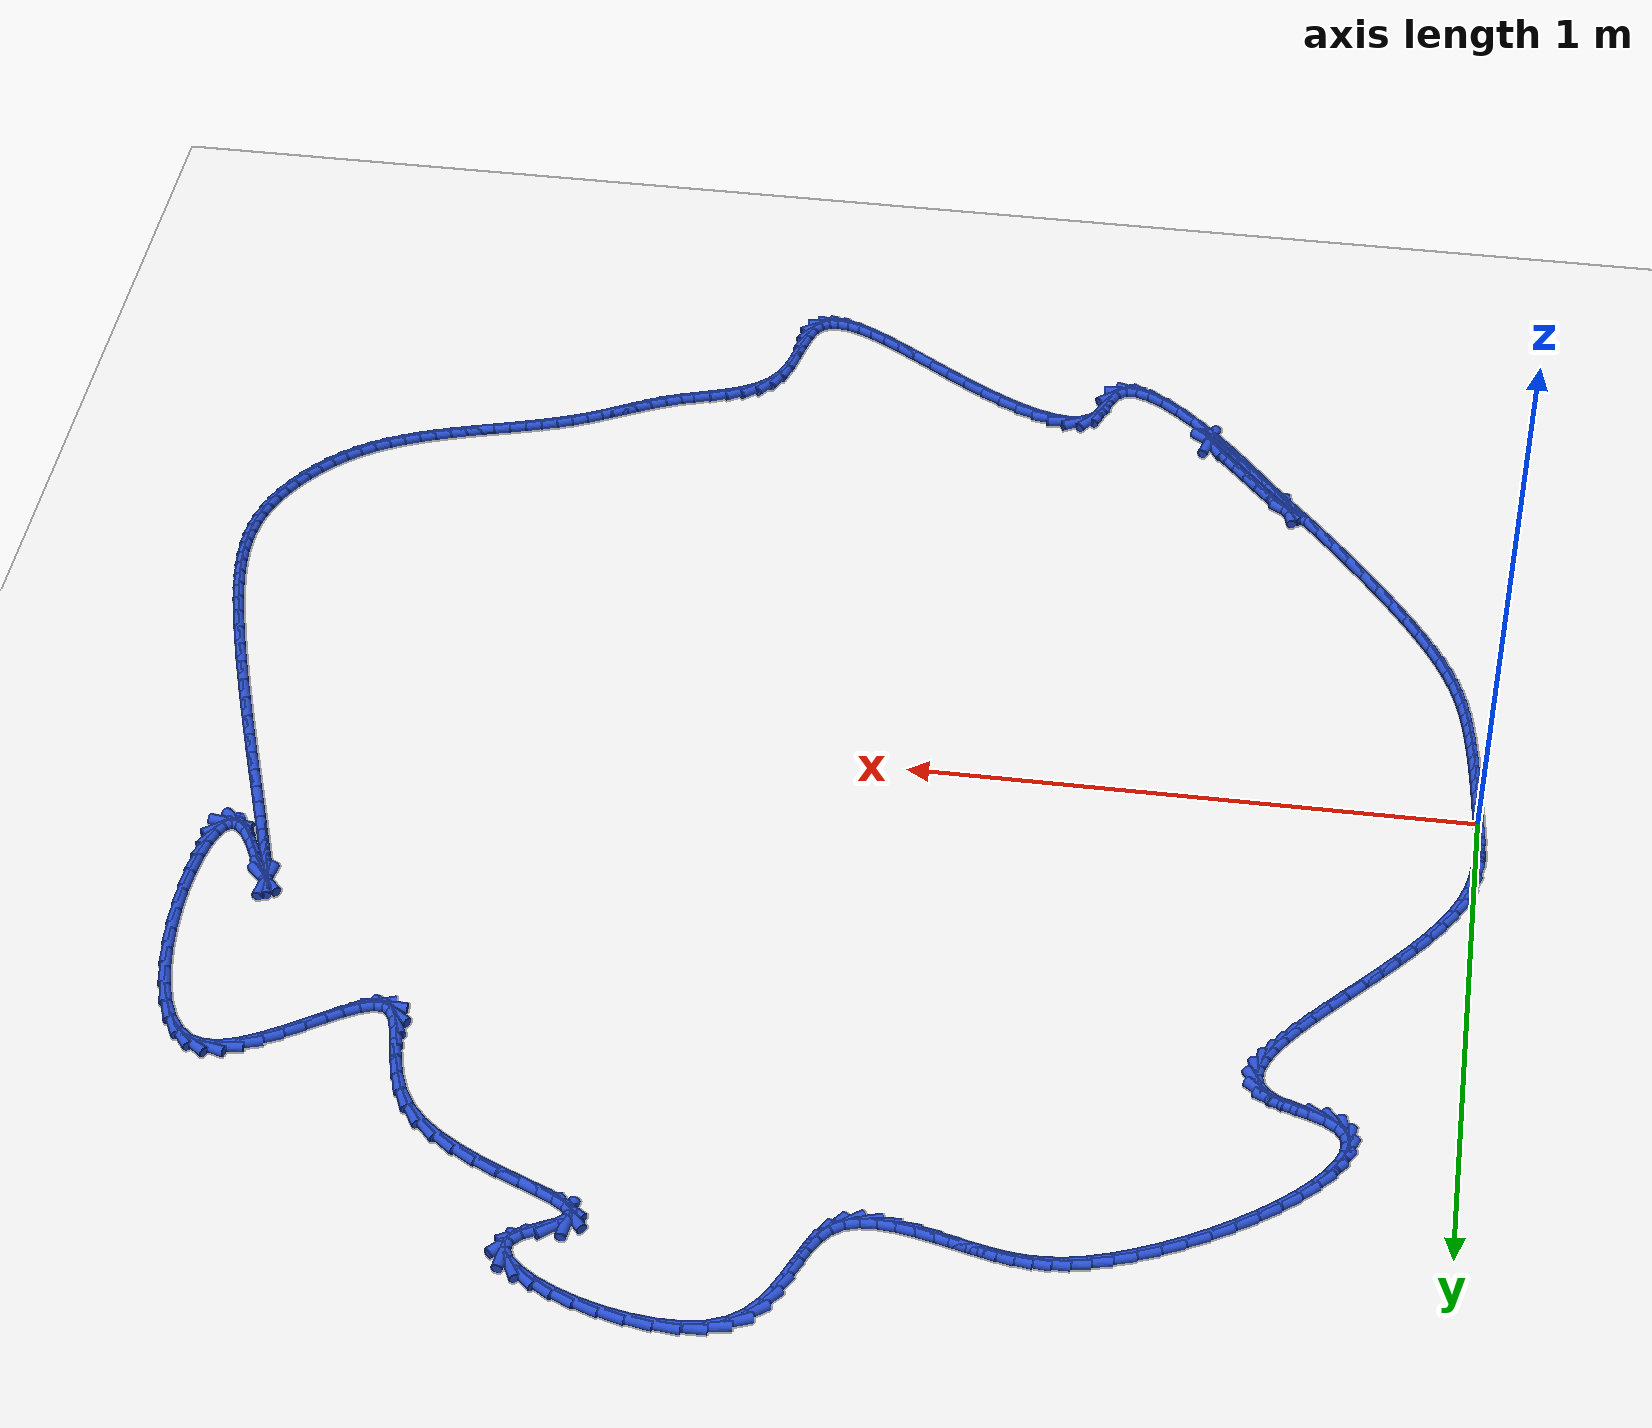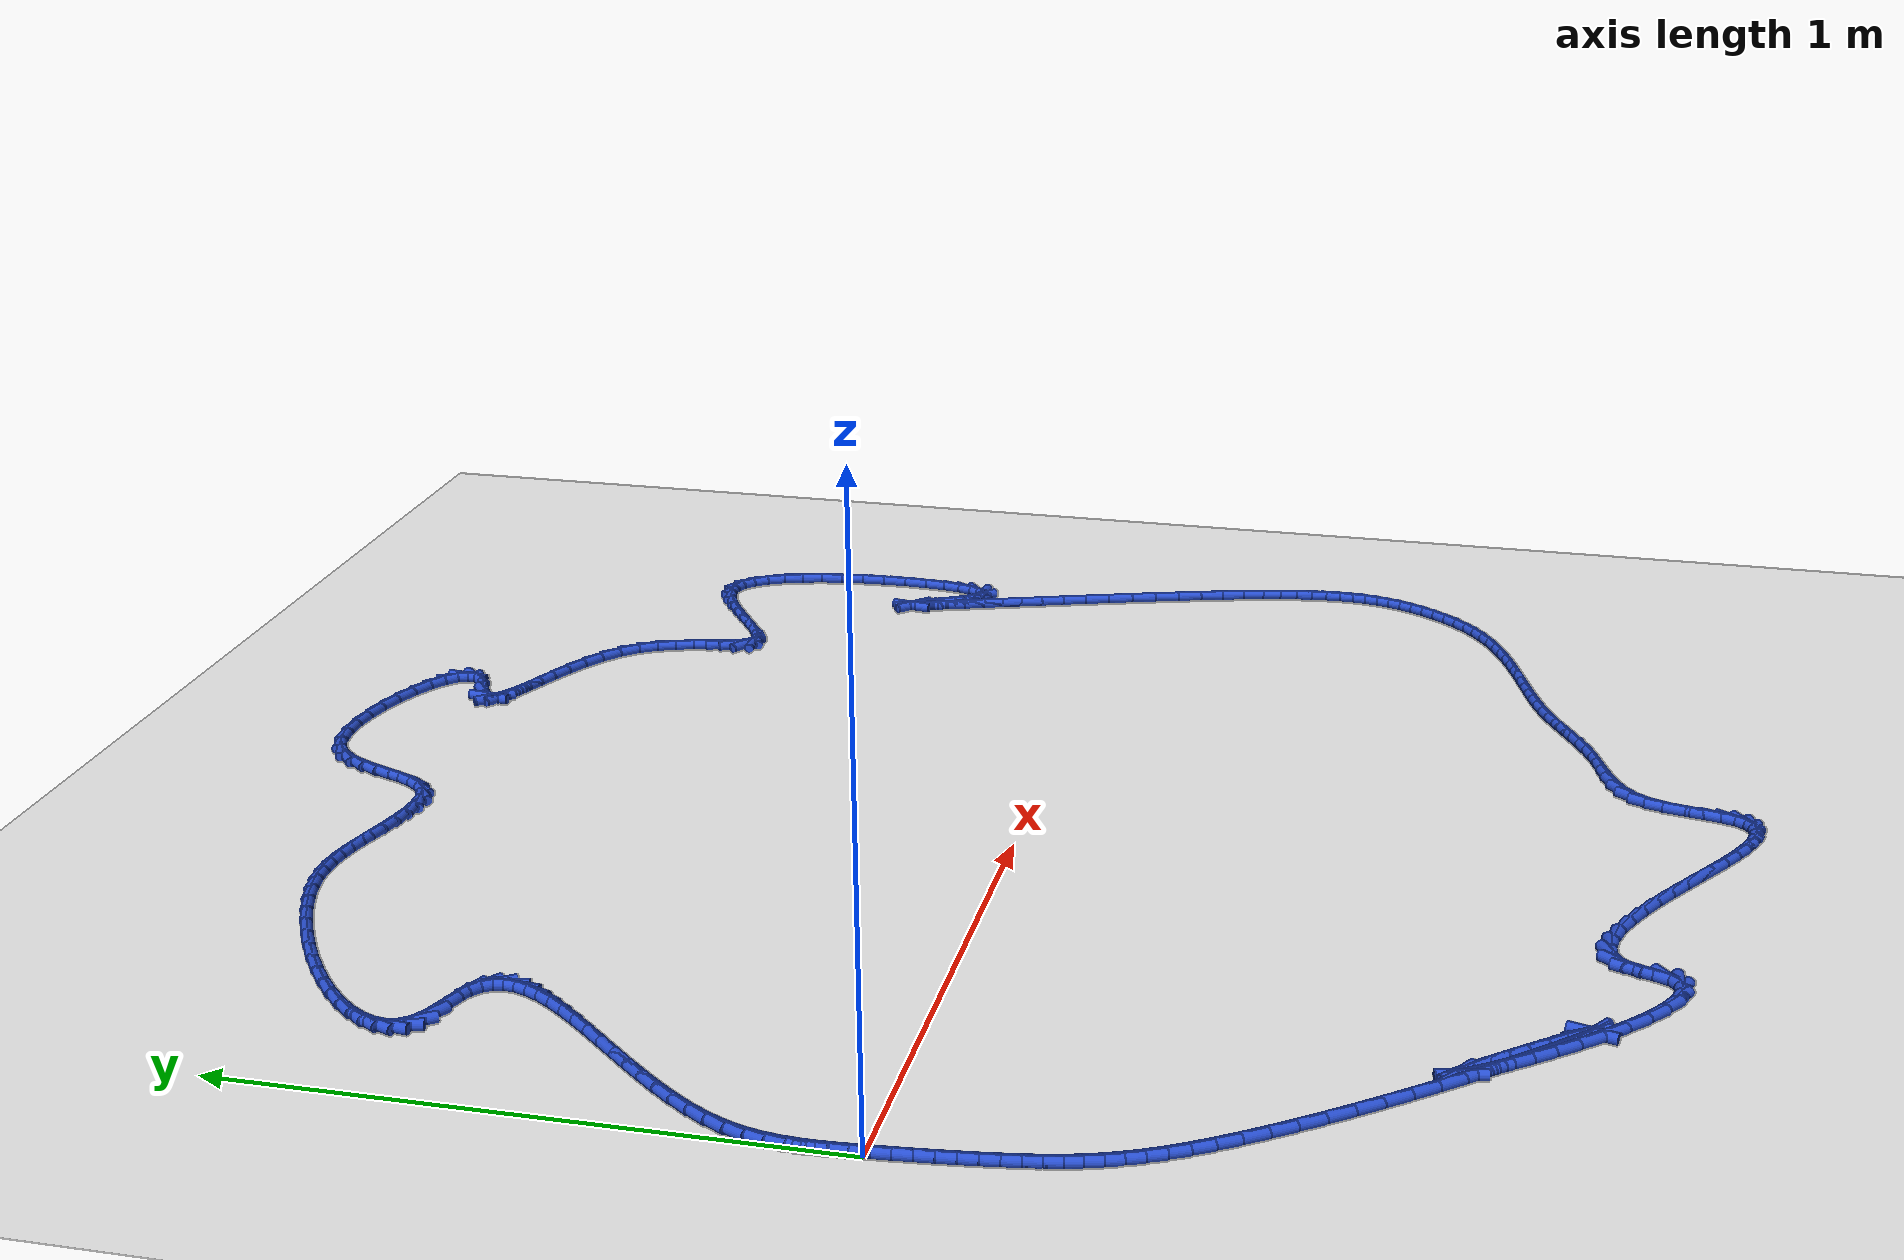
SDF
<sdf version="1.6">
 <world name="default">
  <light name="sun" type="directional">
   <pose>0 0 10 0 -0 0</pose>
   <diffuse>0.8 0.8 0.8 1</diffuse>
   <specular>0.2 0.2 0.2 1</specular>
   <attenuation>
    <range>1000</range>
    <constant>0.9</constant>
    <linear>0.01</linear>
    <quadratic>0.001</quadratic>
   </attenuation>
   <direction>-0.5 0.1 -0.9</direction>
  </light>
  <model name="ground_plane">
   <static>1</static>
   <link name="link">
    <collision name="collision">
     <geometry><plane><normal>0 0 1</normal><size>100 100</size></plane></geometry>
     <surface><friction><ode><mu>100</mu><mu2>50</mu2></ode></friction></surface>
    </collision>
    <visual name="visual">
     <cast_shadows>0</cast_shadows>
     <geometry><plane><normal>0 0 1</normal><size>100 100</size></plane></geometry>
     <material>
      <script><uri>file://media/materials/scripts/gazebo.material</uri><name>Gazebo/WhiteGlow</name></script>
     </material>
    </visual>
   </link>
  </model>
  <gravity>0 0 -9.8</gravity>
  <magnetic_field>6e-06 2.3e-05 -4.2e-05</magnetic_field>
  <atmosphere type="adiabatic"/>
  <physics name="default_physics" default="0" type="ode">
   <max_step_size>0.001</max_step_size>
   <real_time_factor>1</real_time_factor>
   <real_time_update_rate>1000</real_time_update_rate>
  </physics>
  <scene><ambient>0.4 0.4 0.4 1</ambient><background>0.7 0.7 0.7 1</background><shadows>1</shadows></scene>
  <spherical_coordinates>
   <surface_model>EARTH_WGS84</surface_model>
   <latitude_deg>0</latitude_deg>
   <longitude_deg>0</longitude_deg>
   <elevation>0</elevation>
   <heading_deg>0</heading_deg>
  </spherical_coordinates>
  <model name="line">
   <link name="link_0">
    <pose>4.336808689942018e-18 -1.3877787807814457e-17 0.01 0 1.57 -1.5004727236645181</pose>
    <collision name="collision">
     <geometry><cylinder><radius>0.01</radius><length>0.08</length></cylinder></geometry>
    </collision>
    <visual name="visual">
     <material>
      <script><name>Gazebo/Blue</name><uri>file://media/materials/scripts/gazebo.material</uri></script>
     </material>
     <geometry><cylinder><radius>0.01</radius><length>0.08</length></cylinder></geometry>
    </visual>
   </link>
   <link name="link_1">
    <pose>-0.002090213842050008 0.02967377890762394 0.01 0 1.57 -1.5243912335666294</pose>
    <collision name="collision">
     <geometry><cylinder><radius>0.01</radius><length>0.08</length></cylinder></geometry>
    </collision>
    <visual name="visual">
     <material>
      <script><name>Gazebo/Blue</name><uri>file://media/materials/scripts/gazebo.material</uri></script>
     </material>
     <geometry><cylinder><radius>0.01</radius><length>0.08</length></cylinder></geometry>
    </visual>
   </link>
   <link name="link_2">
    <pose>-0.003456920320375669 0.059104283312430735 0.01 0 1.57 -1.5678988701776204</pose>
    <collision name="collision">
     <geometry><cylinder><radius>0.01</radius><length>0.08</length></cylinder></geometry>
    </collision>
    <visual name="visual">
     <material>
      <script><name>Gazebo/Blue</name><uri>file://media/materials/scripts/gazebo.material</uri></script>
     </material>
     <geometry><cylinder><radius>0.01</radius><length>0.08</length></cylinder></geometry>
    </visual>
   </link>
   <link name="link_3">
    <pose>-0.003541878716738143 0.0884259159838732 0.01 0 1.57 1.5110650794174934</pose>
    <collision name="collision">
     <geometry><cylinder><radius>0.01</radius><length>0.08</length></cylinder></geometry>
    </collision>
    <visual name="visual">
     <material>
      <script><name>Gazebo/Blue</name><uri>file://media/materials/scripts/gazebo.material</uri></script>
     </material>
     <geometry><cylinder><radius>0.01</radius><length>0.08</length></cylinder></geometry>
    </visual>
   </link>
   <link name="link_4">
    <pose>-0.0017868483128985852 0.11777307969140406 0.01 0 1.57 1.4309603608351413</pose>
    <collision name="collision">
     <geometry><cylinder><radius>0.01</radius><length>0.08</length></cylinder></geometry>
    </collision>
    <visual name="visual">
     <material>
      <script><name>Gazebo/Blue</name><uri>file://media/materials/scripts/gazebo.material</uri></script>
     </material>
     <geometry><cylinder><radius>0.01</radius><length>0.08</length></cylinder></geometry>
    </visual>
   </link>
   <link name="link_5">
    <pose>0.002366411609381844 0.14728017720447614 0.01 0 1.57 1.3366038377642835</pose>
    <collision name="collision">
     <geometry><cylinder><radius>0.01</radius><length>0.08</length></cylinder></geometry>
    </collision>
    <visual name="visual">
     <material>
      <script><name>Gazebo/Blue</name><uri>file://media/materials/scripts/gazebo.material</uri></script>
     </material>
     <geometry><cylinder><radius>0.01</radius><length>0.08</length></cylinder></geometry>
    </visual>
   </link>
   <link name="link_6">
    <pose>0.009476141768341979 0.17708161129254213 0.01 0 1.57 1.2328289585889005</pose>
    <collision name="collision">
     <geometry><cylinder><radius>0.01</radius><length>0.08</length></cylinder></geometry>
    </collision>
    <visual name="visual">
     <material>
      <script><name>Gazebo/Blue</name><uri>file://media/materials/scripts/gazebo.material</uri></script>
     </material>
     <geometry><cylinder><radius>0.01</radius><length>0.08</length></cylinder></geometry>
    </visual>
   </link>
   <link name="link_7">
    <pose>0.020100582882220674 0.20731178472505488 0.01 0 1.57 1.1274622885355785</pose>
    <collision name="collision">
     <geometry><cylinder><radius>0.01</radius><length>0.08</length></cylinder></geometry>
    </collision>
    <visual name="visual">
     <material>
      <script><name>Gazebo/Blue</name><uri>file://media/materials/scripts/gazebo.material</uri></script>
     </material>
     <geometry><cylinder><radius>0.01</radius><length>0.08</length></cylinder></geometry>
    </visual>
   </link>
   <link name="link_8">
    <pose>0.034712990333967325 0.2380838225575713 0.01 0 1.57 1.040139949571756</pose>
    <collision name="collision">
     <geometry><cylinder><radius>0.01</radius><length>0.08</length></cylinder></geometry>
    </collision>
    <visual name="visual">
     <material>
      <script><name>Gazebo/Blue</name><uri>file://media/materials/scripts/gazebo.material</uri></script>
     </material>
     <geometry><cylinder><radius>0.01</radius><length>0.08</length></cylinder></geometry>
    </visual>
   </link>
   <link name="link_9">
    <pose>0.053045450593195036 0.26932528394733474 0.01 0 1.57 0.974633105736349</pose>
    <collision name="collision">
     <geometry><cylinder><radius>0.01</radius><length>0.08</length></cylinder></geometry>
    </collision>
    <visual name="visual">
     <material>
      <script><name>Gazebo/Blue</name><uri>file://media/materials/scripts/gazebo.material</uri></script>
     </material>
     <geometry><cylinder><radius>0.01</radius><length>0.08</length></cylinder></geometry>
    </visual>
   </link>
   <link name="link_10">
    <pose>0.07444779799339217 0.30086802387438144 0.01 0 1.57 0.9260319252170768</pose>
    <collision name="collision">
     <geometry><cylinder><radius>0.01</radius><length>0.08</length></cylinder></geometry>
    </collision>
    <visual name="visual">
     <material>
      <script><name>Gazebo/Blue</name><uri>file://media/materials/scripts/gazebo.material</uri></script>
     </material>
     <geometry><cylinder><radius>0.01</radius><length>0.08</length></cylinder></geometry>
    </visual>
   </link>
   <link name="link_11">
    <pose>0.09826668894050022 0.33254310166343964 0.01 0 1.57 0.8908483429197153</pose>
    <collision name="collision">
     <geometry><cylinder><radius>0.01</radius><length>0.08</length></cylinder></geometry>
    </collision>
    <visual name="visual">
     <material>
      <script><name>Gazebo/Blue</name><uri>file://media/materials/scripts/gazebo.material</uri></script>
     </material>
     <geometry><cylinder><radius>0.01</radius><length>0.08</length></cylinder></geometry>
    </visual>
   </link>
   <link name="link_12">
    <pose>0.12384877984046072 0.3641815766392376 0.01 0 1.57 0.8667834890952345</pose>
    <collision name="collision">
     <geometry><cylinder><radius>0.01</radius><length>0.08</length></cylinder></geometry>
    </collision>
    <visual name="visual">
     <material>
      <script><name>Gazebo/Blue</name><uri>file://media/materials/scripts/gazebo.material</uri></script>
     </material>
     <geometry><cylinder><radius>0.01</radius><length>0.08</length></cylinder></geometry>
    </visual>
   </link>
   <link name="link_13">
    <pose>0.1505407270992152 0.3956145081265039 0.01 0 1.57 0.8524713388586628</pose>
    <collision name="collision">
     <geometry><cylinder><radius>0.01</radius><length>0.08</length></cylinder></geometry>
    </collision>
    <visual name="visual">
     <material>
      <script><name>Gazebo/Blue</name><uri>file://media/materials/scripts/gazebo.material</uri></script>
     </material>
     <geometry><cylinder><radius>0.01</radius><length>0.08</length></cylinder></geometry>
    </visual>
   </link>
   <link name="link_14">
    <pose>0.17768918712270512 0.42667295544996653 0.01 0 1.57 0.8473268928034431</pose>
    <collision name="collision">
     <geometry><cylinder><radius>0.01</radius><length>0.08</length></cylinder></geometry>
    </collision>
    <visual name="visual">
     <material>
      <script><name>Gazebo/Blue</name><uri>file://media/materials/scripts/gazebo.material</uri></script>
     </material>
     <geometry><cylinder><radius>0.01</radius><length>0.08</length></cylinder></geometry>
    </visual>
   </link>
   <link name="link_15">
    <pose>0.204640816316872 0.4571879779343539 0.01 0 1.57 0.8515079444819507</pose>
    <collision name="collision">
     <geometry><cylinder><radius>0.01</radius><length>0.08</length></cylinder></geometry>
    </collision>
    <visual name="visual">
     <material>
      <script><name>Gazebo/Blue</name><uri>file://media/materials/scripts/gazebo.material</uri></script>
     </material>
     <geometry><cylinder><radius>0.01</radius><length>0.08</length></cylinder></geometry>
    </visual>
   </link>
   <link name="link_16">
    <pose>0.23074227108765738 0.48699063490439426 0.01 0 1.57 0.8660054793066367</pose>
    <collision name="collision">
     <geometry><cylinder><radius>0.01</radius><length>0.08</length></cylinder></geometry>
    </collision>
    <visual name="visual">
     <material>
      <script><name>Gazebo/Blue</name><uri>file://media/materials/scripts/gazebo.material</uri></script>
     </material>
     <geometry><cylinder><radius>0.01</radius><length>0.08</length></cylinder></geometry>
    </visual>
   </link>
   <link name="link_17">
    <pose>0.25534020784100275 0.5159119856848159 0.01 0 1.57 0.8929087442363446</pose>
    <collision name="collision">
     <geometry><cylinder><radius>0.01</radius><length>0.08</length></cylinder></geometry>
    </collision>
    <visual name="visual">
     <material>
      <script><name>Gazebo/Blue</name><uri>file://media/materials/scripts/gazebo.material</uri></script>
     </material>
     <geometry><cylinder><radius>0.01</radius><length>0.08</length></cylinder></geometry>
    </visual>
   </link>
   <link name="link_18">
    <pose>0.2777812829828497 0.5437830896003473 0.01 0 1.57 0.9359491832190968</pose>
    <collision name="collision">
     <geometry><cylinder><radius>0.01</radius><length>0.08</length></cylinder></geometry>
    </collision>
    <visual name="visual">
     <material>
      <script><name>Gazebo/Blue</name><uri>file://media/materials/scripts/gazebo.material</uri></script>
     </material>
     <geometry><cylinder><radius>0.01</radius><length>0.08</length></cylinder></geometry>
    </visual>
   </link>
   <link name="link_19">
    <pose>0.2974121529191396 0.5704350059757165 0.01 0 1.57 1.0015253499262218</pose>
    <collision name="collision">
     <geometry><cylinder><radius>0.01</radius><length>0.08</length></cylinder></geometry>
    </collision>
    <visual name="visual">
     <material>
      <script><name>Gazebo/Blue</name><uri>file://media/materials/scripts/gazebo.material</uri></script>
     </material>
     <geometry><cylinder><radius>0.01</radius><length>0.08</length></cylinder></geometry>
    </visual>
   </link>
   <link name="link_20">
    <pose>0.3135794740558142 0.5956987941356519 0.01 0 1.57 1.1005206180244087</pose>
    <collision name="collision">
     <geometry><cylinder><radius>0.01</radius><length>0.08</length></cylinder></geometry>
    </collision>
    <visual name="visual">
     <material>
      <script><name>Gazebo/Blue</name><uri>file://media/materials/scripts/gazebo.material</uri></script>
     </material>
     <geometry><cylinder><radius>0.01</radius><length>0.08</length></cylinder></geometry>
    </visual>
   </link>
   <link name="link_21">
    <pose>0.3256299027988147 0.6194055134048818 0.01 0 1.57 1.250959550366497</pose>
    <collision name="collision">
     <geometry><cylinder><radius>0.01</radius><length>0.08</length></cylinder></geometry>
    </collision>
    <visual name="visual">
     <material>
      <script><name>Gazebo/Blue</name><uri>file://media/materials/scripts/gazebo.material</uri></script>
     </material>
     <geometry><cylinder><radius>0.01</radius><length>0.08</length></cylinder></geometry>
    </visual>
   </link>
   <link name="link_22">
    <pose>0.33291009555408285 0.6413862231081344 0.01 0 1.57 1.4786239385223316</pose>
    <collision name="collision">
     <geometry><cylinder><radius>0.01</radius><length>0.08</length></cylinder></geometry>
    </collision>
    <visual name="visual">
     <material>
      <script><name>Gazebo/Blue</name><uri>file://media/materials/scripts/gazebo.material</uri></script>
     </material>
     <geometry><cylinder><radius>0.01</radius><length>0.08</length></cylinder></geometry>
    </visual>
   </link>
   <link name="link_23">
    <pose>0.33476670872756 0.6614719825701381 0.01 0 1.57 -1.3407642855303261</pose>
    <collision name="collision">
     <geometry><cylinder><radius>0.01</radius><length>0.08</length></cylinder></geometry>
    </collision>
    <visual name="visual">
     <material>
      <script><name>Gazebo/Blue</name><uri>file://media/materials/scripts/gazebo.material</uri></script>
     </material>
     <geometry><cylinder><radius>0.01</radius><length>0.08</length></cylinder></geometry>
    </visual>
   </link>
   <link name="link_24">
    <pose>0.3305463987251878 0.6794938511156213 0.01 0 1.57 -0.9644084942905469</pose>
    <collision name="collision">
     <geometry><cylinder><radius>0.01</radius><length>0.08</length></cylinder></geometry>
    </collision>
    <visual name="visual">
     <material>
      <script><name>Gazebo/Blue</name><uri>file://media/materials/scripts/gazebo.material</uri></script>
     </material>
     <geometry><cylinder><radius>0.01</radius><length>0.08</length></cylinder></geometry>
    </visual>
   </link>
   <link name="link_25">
    <pose>0.3195958219529077 0.6952828880693122 0.01 0 1.57 -0.630695453520344</pose>
    <collision name="collision">
     <geometry><cylinder><radius>0.01</radius><length>0.08</length></cylinder></geometry>
    </collision>
    <visual name="visual">
     <material>
      <script><name>Gazebo/Blue</name><uri>file://media/materials/scripts/gazebo.material</uri></script>
     </material>
     <geometry><cylinder><radius>0.01</radius><length>0.08</length></cylinder></geometry>
    </visual>
   </link>
   <link name="link_26">
    <pose>0.3012616348166613 0.7086701527559389 0.01 0 1.57 -0.40079031758931793</pose>
    <collision name="collision">
     <geometry><cylinder><radius>0.01</radius><length>0.08</length></cylinder></geometry>
    </collision>
    <visual name="visual">
     <material>
      <script><name>Gazebo/Blue</name><uri>file://media/materials/scripts/gazebo.material</uri></script>
     </material>
     <geometry><cylinder><radius>0.01</radius><length>0.08</length></cylinder></geometry>
    </visual>
   </link>
   <link name="link_27">
    <pose>0.27535995974188815 0.7196453431461279 0.01 0 1.57 -0.32118776552928446</pose>
    <collision name="collision">
     <geometry><cylinder><radius>0.01</radius><length>0.08</length></cylinder></geometry>
    </collision>
    <visual name="visual">
     <material>
      <script><name>Gazebo/Blue</name><uri>file://media/materials/scripts/gazebo.material</uri></script>
     </material>
     <geometry><cylinder><radius>0.01</radius><length>0.08</length></cylinder></geometry>
    </visual>
   </link>
   <link name="link_28">
    <pose>0.24564927381471666 0.7295303298897782 0.01 0 1.57 -0.370110753486321</pose>
    <collision name="collision">
     <geometry><cylinder><radius>0.01</radius><length>0.08</length></cylinder></geometry>
    </collision>
    <visual name="visual">
     <material>
      <script><name>Gazebo/Blue</name><uri>file://media/materials/scripts/gazebo.material</uri></script>
     </material>
     <geometry><cylinder><radius>0.01</radius><length>0.08</length></cylinder></geometry>
    </visual>
   </link>
   <link name="link_29">
    <pose>0.21785859035713234 0.7403128533422965 0.01 0 1.57 -0.5789276305539273</pose>
    <collision name="collision">
     <geometry><cylinder><radius>0.01</radius><length>0.08</length></cylinder></geometry>
    </collision>
    <visual name="visual">
     <material>
      <script><name>Gazebo/Blue</name><uri>file://media/materials/scripts/gazebo.material</uri></script>
     </material>
     <geometry><cylinder><radius>0.01</radius><length>0.08</length></cylinder></geometry>
    </visual>
   </link>
   <link name="link_30">
    <pose>0.19722996862845044 0.7537964805623706 0.01 0 1.57 -0.933395760136652</pose>
    <collision name="collision">
     <geometry><cylinder><radius>0.01</radius><length>0.08</length></cylinder></geometry>
    </collision>
    <visual name="visual">
     <material>
      <script><name>Gazebo/Blue</name><uri>file://media/materials/scripts/gazebo.material</uri></script>
     </material>
     <geometry><cylinder><radius>0.01</radius><length>0.08</length></cylinder></geometry>
    </visual>
   </link>
   <link name="link_31">
    <pose>0.18502171263524067 0.7702827349066502 0.01 0 1.57 -1.3426103056390835</pose>
    <collision name="collision">
     <geometry><cylinder><radius>0.01</radius><length>0.08</length></cylinder></geometry>
    </collision>
    <visual name="visual">
     <material>
      <script><name>Gazebo/Blue</name><uri>file://media/materials/scripts/gazebo.material</uri></script>
     </material>
     <geometry><cylinder><radius>0.01</radius><length>0.08</length></cylinder></geometry>
    </visual>
   </link>
   <link name="link_32">
    <pose>0.1805921367438082 0.789356763525912 0.01 0 1.57 1.4445694586497135</pose>
    <collision name="collision">
     <geometry><cylinder><radius>0.01</radius><length>0.08</length></cylinder></geometry>
    </collision>
    <visual name="visual">
     <material>
      <script><name>Gazebo/Blue</name><uri>file://media/materials/scripts/gazebo.material</uri></script>
     </material>
     <geometry><cylinder><radius>0.01</radius><length>0.08</length></cylinder></geometry>
    </visual>
   </link>
   <link name="link_33">
    <pose>0.1832878478669804 0.8105992993673352 0.01 0 1.57 1.19138172134711</pose>
    <collision name="collision">
     <geometry><cylinder><radius>0.01</radius><length>0.08</length></cylinder></geometry>
    </collision>
    <visual name="visual">
     <material>
      <script><name>Gazebo/Blue</name><uri>file://media/materials/scripts/gazebo.material</uri></script>
     </material>
     <geometry><cylinder><radius>0.01</radius><length>0.08</length></cylinder></geometry>
    </visual>
   </link>
   <link name="link_34">
    <pose>0.19245545291758462 0.8335910753780997 0.01 0 1.57 1.0185786303793594</pose>
    <collision name="collision">
     <geometry><cylinder><radius>0.01</radius><length>0.08</length></cylinder></geometry>
    </collision>
    <visual name="visual">
     <material>
      <script><name>Gazebo/Blue</name><uri>file://media/materials/scripts/gazebo.material</uri></script>
     </material>
     <geometry><cylinder><radius>0.01</radius><length>0.08</length></cylinder></geometry>
    </visual>
   </link>
   <link name="link_35">
    <pose>0.20744155880844828 0.8579128245053855 0.01 0 1.57 0.8968957139933799</pose>
    <collision name="collision">
     <geometry><cylinder><radius>0.01</radius><length>0.08</length></cylinder></geometry>
    </collision>
    <visual name="visual">
     <material>
      <script><name>Gazebo/Blue</name><uri>file://media/materials/scripts/gazebo.material</uri></script>
     </material>
     <geometry><cylinder><radius>0.01</radius><length>0.08</length></cylinder></geometry>
    </visual>
   </link>
   <link name="link_36">
    <pose>0.22759277245239876 0.883145279696372 0.01 0 1.57 0.8064514682048279</pose>
    <collision name="collision">
     <geometry><cylinder><radius>0.01</radius><length>0.08</length></cylinder></geometry>
    </collision>
    <visual name="visual">
     <material>
      <script><name>Gazebo/Blue</name><uri>file://media/materials/scripts/gazebo.material</uri></script>
     </material>
     <geometry><cylinder><radius>0.01</radius><length>0.08</length></cylinder></geometry>
    </visual>
   </link>
   <link name="link_37">
    <pose>0.2522557007622635 0.908869173898239 0.01 0 1.57 0.7352686507906886</pose>
    <collision name="collision">
     <geometry><cylinder><radius>0.01</radius><length>0.08</length></cylinder></geometry>
    </collision>
    <visual name="visual">
     <material>
      <script><name>Gazebo/Blue</name><uri>file://media/materials/scripts/gazebo.material</uri></script>
     </material>
     <geometry><cylinder><radius>0.01</radius><length>0.08</length></cylinder></geometry>
    </visual>
   </link>
   <link name="link_38">
    <pose>0.2807769506508697 0.9346652400581662 0.01 0 1.57 0.6760470353094248</pose>
    <collision name="collision">
     <geometry><cylinder><radius>0.01</radius><length>0.08</length></cylinder></geometry>
    </collision>
    <visual name="visual">
     <material>
      <script><name>Gazebo/Blue</name><uri>file://media/materials/scripts/gazebo.material</uri></script>
     </material>
     <geometry><cylinder><radius>0.01</radius><length>0.08</length></cylinder></geometry>
    </visual>
   </link>
   <link name="link_39">
    <pose>0.31250312903104516 0.9601142111233334 0.01 0 1.57 0.6240740622735509</pose>
    <collision name="collision">
     <geometry><cylinder><radius>0.01</radius><length>0.08</length></cylinder></geometry>
    </collision>
    <visual name="visual">
     <material>
      <script><name>Gazebo/Blue</name><uri>file://media/materials/scripts/gazebo.material</uri></script>
     </material>
     <geometry><cylinder><radius>0.01</radius><length>0.08</length></cylinder></geometry>
    </visual>
   </link>
   <link name="link_40">
    <pose>0.346780842815617 0.9847968200409205 0.01 0 1.57 0.5760384446696214</pose>
    <collision name="collision">
     <geometry><cylinder><radius>0.01</radius><length>0.08</length></cylinder></geometry>
    </collision>
    <visual name="visual">
     <material>
      <script><name>Gazebo/Blue</name><uri>file://media/materials/scripts/gazebo.material</uri></script>
     </material>
     <geometry><cylinder><radius>0.01</radius><length>0.08</length></cylinder></geometry>
    </visual>
   </link>
   <link name="link_41">
    <pose>0.3829566989174125 1.0082937997581067 0.01 0 1.57 0.529337563380191</pose>
    <collision name="collision">
     <geometry><cylinder><radius>0.01</radius><length>0.08</length></cylinder></geometry>
    </collision>
    <visual name="visual">
     <material>
      <script><name>Gazebo/Blue</name><uri>file://media/materials/scripts/gazebo.material</uri></script>
     </material>
     <geometry><cylinder><radius>0.01</radius><length>0.08</length></cylinder></geometry>
    </visual>
   </link>
   <link name="link_42">
    <pose>0.42037730424925923 1.0301858832220723 0.01 0 1.57 0.48162299784644824</pose>
    <collision name="collision">
     <geometry><cylinder><radius>0.01</radius><length>0.08</length></cylinder></geometry>
    </collision>
    <visual name="visual">
     <material>
      <script><name>Gazebo/Blue</name><uri>file://media/materials/scripts/gazebo.material</uri></script>
     </material>
     <geometry><cylinder><radius>0.01</radius><length>0.08</length></cylinder></geometry>
    </visual>
   </link>
   <link name="link_43">
    <pose>0.4583892657239844 1.0500538033799964 0.01 0 1.57 0.43043221737695614</pose>
    <collision name="collision">
     <geometry><cylinder><radius>0.01</radius><length>0.08</length></cylinder></geometry>
    </collision>
    <visual name="visual">
     <material>
      <script><name>Gazebo/Blue</name><uri>file://media/materials/scripts/gazebo.material</uri></script>
     </material>
     <geometry><cylinder><radius>0.01</radius><length>0.08</length></cylinder></geometry>
    </visual>
   </link>
   <link name="link_44">
    <pose>0.49633919025441575 1.0674782931790592 0.01 0 1.57 0.3727960911620906</pose>
    <collision name="collision">
     <geometry><cylinder><radius>0.01</radius><length>0.08</length></cylinder></geometry>
    </collision>
    <visual name="visual">
     <material>
      <script><name>Gazebo/Blue</name><uri>file://media/materials/scripts/gazebo.material</uri></script>
     </material>
     <geometry><cylinder><radius>0.01</radius><length>0.08</length></cylinder></geometry>
    </visual>
   </link>
   <link name="link_45">
    <pose>0.5335736847533803 1.0820400855664403 0.01 0 1.57 0.3047077780259162</pose>
    <collision name="collision">
     <geometry><cylinder><radius>0.01</radius><length>0.08</length></cylinder></geometry>
    </collision>
    <visual name="visual">
     <material>
      <script><name>Gazebo/Blue</name><uri>file://media/materials/scripts/gazebo.material</uri></script>
     </material>
     <geometry><cylinder><radius>0.01</radius><length>0.08</length></cylinder></geometry>
    </visual>
   </link>
   <link name="link_46">
    <pose>0.5694393561337056 1.0933199134893197 0.01 0 1.57 0.22032367388659238</pose>
    <collision name="collision">
     <geometry><cylinder><radius>0.01</radius><length>0.08</length></cylinder></geometry>
    </collision>
    <visual name="visual">
     <material>
      <script><name>Gazebo/Blue</name><uri>file://media/materials/scripts/gazebo.material</uri></script>
     </material>
     <geometry><cylinder><radius>0.01</radius><length>0.08</length></cylinder></geometry>
    </visual>
   </link>
   <link name="link_47">
    <pose>0.6032847010396489 1.1008998934302017 0.01 0 1.57 0.11801092920639973</pose>
    <collision name="collision">
     <geometry><cylinder><radius>0.01</radius><length>0.08</length></cylinder></geometry>
    </collision>
    <visual name="visual">
     <material>
      <script><name>Gazebo/Blue</name><uri>file://media/materials/scripts/gazebo.material</uri></script>
     </material>
     <geometry><cylinder><radius>0.01</radius><length>0.08</length></cylinder></geometry>
    </visual>
   </link>
   <link name="link_48">
    <pose>0.6348391668142684 1.1046410485673424 0.01 0 1.57 0.012693178703625338</pose>
    <collision name="collision">
     <geometry><cylinder><radius>0.01</radius><length>0.08</length></cylinder></geometry>
    </collision>
    <visual name="visual">
     <material>
      <script><name>Gazebo/Blue</name><uri>file://media/materials/scripts/gazebo.material</uri></script>
     </material>
     <geometry><cylinder><radius>0.01</radius><length>0.08</length></cylinder></geometry>
    </visual>
   </link>
   <link name="link_49">
    <pose>0.6646726885117425 1.1050197511282718 0.01 0 1.57 -0.08402460405793628</pose>
    <collision name="collision">
     <geometry><cylinder><radius>0.01</radius><length>0.08</length></cylinder></geometry>
    </collision>
    <visual name="visual">
     <material>
      <script><name>Gazebo/Blue</name><uri>file://media/materials/scripts/gazebo.material</uri></script>
     </material>
     <geometry><cylinder><radius>0.01</radius><length>0.08</length></cylinder></geometry>
    </visual>
   </link>
   <link name="link_50">
    <pose>0.6934674723057194 1.1025945707667442 0.01 0 1.57 -0.16277965578552236</pose>
    <collision name="collision">
     <geometry><cylinder><radius>0.01</radius><length>0.08</length></cylinder></geometry>
    </collision>
    <visual name="visual">
     <material>
      <script><name>Gazebo/Blue</name><uri>file://media/materials/scripts/gazebo.material</uri></script>
     </material>
     <geometry><cylinder><radius>0.01</radius><length>0.08</length></cylinder></geometry>
    </visual>
   </link>
   <link name="link_51">
    <pose>0.7219057243698467 1.0979240771365126 0.01 0 1.57 -0.21751751214565163</pose>
    <collision name="collision">
     <geometry><cylinder><radius>0.01</radius><length>0.08</length></cylinder></geometry>
    </collision>
    <visual name="visual">
     <material>
      <script><name>Gazebo/Blue</name><uri>file://media/materials/scripts/gazebo.material</uri></script>
     </material>
     <geometry><cylinder><radius>0.01</radius><length>0.08</length></cylinder></geometry>
    </visual>
   </link>
   <link name="link_52">
    <pose>0.750669650877773 1.0915668398913312 0.01 0 1.57 -0.24632048232726458</pose>
    <collision name="collision">
     <geometry><cylinder><radius>0.01</radius><length>0.08</length></cylinder></geometry>
    </collision>
    <visual name="visual">
     <material>
      <script><name>Gazebo/Blue</name><uri>file://media/materials/scripts/gazebo.material</uri></script>
     </material>
     <geometry><cylinder><radius>0.01</radius><length>0.08</length></cylinder></geometry>
    </visual>
   </link>
   <link name="link_53">
    <pose>0.7804414580031465 1.084081428684954 0.01 0 1.57 -0.25017010120863326</pose>
    <collision name="collision">
     <geometry><cylinder><radius>0.01</radius><length>0.08</length></cylinder></geometry>
    </collision>
    <visual name="visual">
     <material>
      <script><name>Gazebo/Blue</name><uri>file://media/materials/scripts/gazebo.material</uri></script>
     </material>
     <geometry><cylinder><radius>0.01</radius><length>0.08</length></cylinder></geometry>
    </visual>
   </link>
   <link name="link_54">
    <pose>0.8118053019014472 1.076067241411311 0.01 0 1.57 -0.22681612454320704</pose>
    <collision name="collision">
     <geometry><cylinder><radius>0.01</radius><length>0.08</length></cylinder></geometry>
    </collision>
    <visual name="visual">
     <material>
      <script><name>Gazebo/Blue</name><uri>file://media/materials/scripts/gazebo.material</uri></script>
     </material>
     <geometry><cylinder><radius>0.01</radius><length>0.08</length></cylinder></geometry>
    </visual>
   </link>
   <link name="link_55">
    <pose>0.8442519631030452 1.068578959945497 0.01 0 1.57 -0.1721664641101937</pose>
    <collision name="collision">
     <geometry><cylinder><radius>0.01</radius><length>0.08</length></cylinder></geometry>
    </collision>
    <visual name="visual">
     <material>
      <script><name>Gazebo/Blue</name><uri>file://media/materials/scripts/gazebo.material</uri></script>
     </material>
     <geometry><cylinder><radius>0.01</radius><length>0.08</length></cylinder></geometry>
    </visual>
   </link>
   <link name="link_56">
    <pose>0.8765882687766392 1.0629560658254866 0.01 0 1.57 -0.07764772849173787</pose>
    <collision name="collision">
     <geometry><cylinder><radius>0.01</radius><length>0.08</length></cylinder></geometry>
    </collision>
    <visual name="visual">
     <material>
      <script><name>Gazebo/Blue</name><uri>file://media/materials/scripts/gazebo.material</uri></script>
     </material>
     <geometry><cylinder><radius>0.01</radius><length>0.08</length></cylinder></geometry>
    </visual>
   </link>
   <link name="link_57">
    <pose>0.9076105729556858 1.0605424016254794 0.01 0 1.57 0.0749142357881108</pose>
    <collision name="collision">
     <geometry><cylinder><radius>0.01</radius><length>0.08</length></cylinder></geometry>
    </collision>
    <visual name="visual">
     <material>
      <script><name>Gazebo/Blue</name><uri>file://media/materials/scripts/gazebo.material</uri></script>
     </material>
     <geometry><cylinder><radius>0.01</radius><length>0.08</length></cylinder></geometry>
    </visual>
   </link>
   <link name="link_58">
    <pose>0.9361152296736415 1.0626818099196746 0.01 0 1.57 0.3135650039664543</pose>
    <collision name="collision">
     <geometry><cylinder><radius>0.01</radius><length>0.08</length></cylinder></geometry>
    </collision>
    <visual name="visual">
     <material>
      <script><name>Gazebo/Blue</name><uri>file://media/materials/scripts/gazebo.material</uri></script>
     </material>
     <geometry><cylinder><radius>0.01</radius><length>0.08</length></cylinder></geometry>
    </visual>
   </link>
   <link name="link_59">
    <pose>0.9608985929639625 1.0707181332822722 0.01 0 1.57 0.6416438851529567</pose>
    <collision name="collision">
     <geometry><cylinder><radius>0.01</radius><length>0.08</length></cylinder></geometry>
    </collision>
    <visual name="visual">
     <material>
      <script><name>Gazebo/Blue</name><uri>file://media/materials/scripts/gazebo.material</uri></script>
     </material>
     <geometry><cylinder><radius>0.01</radius><length>0.08</length></cylinder></geometry>
    </visual>
   </link>
   <link name="link_60">
    <pose>0.9809882982725167 1.0857271947333158 0.01 0 1.57 0.9226572575720584</pose>
    <collision name="collision">
     <geometry><cylinder><radius>0.01</radius><length>0.08</length></cylinder></geometry>
    </collision>
    <visual name="visual">
     <material>
      <script><name>Gazebo/Blue</name><uri>file://media/materials/scripts/gazebo.material</uri></script>
     </material>
     <geometry><cylinder><radius>0.01</radius><length>0.08</length></cylinder></geometry>
    </visual>
   </link>
   <link name="link_61">
    <pose>0.9970296177038007 1.1069102254200647 0.01 0 1.57 1.093272889969365</pose>
    <collision name="collision">
     <geometry><cylinder><radius>0.01</radius><length>0.08</length></cylinder></geometry>
    </collision>
    <visual name="visual">
     <material>
      <script><name>Gazebo/Blue</name><uri>file://media/materials/scripts/gazebo.material</uri></script>
     </material>
     <geometry><cylinder><radius>0.01</radius><length>0.08</length></cylinder></geometry>
    </visual>
   </link>
   <link name="link_62">
    <pose>1.0103584711677638 1.1326681019996925 0.01 0 1.57 1.1764855130083507</pose>
    <collision name="collision">
     <geometry><cylinder><radius>0.01</radius><length>0.08</length></cylinder></geometry>
    </collision>
    <visual name="visual">
     <material>
      <script><name>Gazebo/Blue</name><uri>file://media/materials/scripts/gazebo.material</uri></script>
     </material>
     <geometry><cylinder><radius>0.01</radius><length>0.08</length></cylinder></geometry>
    </visual>
   </link>
   <link name="link_63">
    <pose>1.0223133638495867 1.1613987051933528 0.01 0 1.57 1.1937614197917494</pose>
    <collision name="collision">
     <geometry><cylinder><radius>0.01</radius><length>0.08</length></cylinder></geometry>
    </collision>
    <visual name="visual">
     <material>
      <script><name>Gazebo/Blue</name><uri>file://media/materials/scripts/gazebo.material</uri></script>
     </material>
     <geometry><cylinder><radius>0.01</radius><length>0.08</length></cylinder></geometry>
    </visual>
   </link>
   <link name="link_64">
    <pose>1.0342328009344484 1.1914999157221984 0.01 0 1.57 1.1540528440105546</pose>
    <collision name="collision">
     <geometry><cylinder><radius>0.01</radius><length>0.08</length></cylinder></geometry>
    </collision>
    <visual name="visual">
     <material>
      <script><name>Gazebo/Blue</name><uri>file://media/materials/scripts/gazebo.material</uri></script>
     </material>
     <geometry><cylinder><radius>0.01</radius><length>0.08</length></cylinder></geometry>
    </visual>
   </link>
   <link name="link_65">
    <pose>1.0474552876075287 1.2213696143073822 0.01 0 1.57 1.055870221673675</pose>
    <collision name="collision">
     <geometry><cylinder><radius>0.01</radius><length>0.08</length></cylinder></geometry>
    </collision>
    <visual name="visual">
     <material>
      <script><name>Gazebo/Blue</name><uri>file://media/materials/scripts/gazebo.material</uri></script>
     </material>
     <geometry><cylinder><radius>0.01</radius><length>0.08</length></cylinder></geometry>
    </visual>
   </link>
   <link name="link_66">
    <pose>1.0633193290540086 1.2494056816700583 0.01 0 1.57 0.8920073400906505</pose>
    <collision name="collision">
     <geometry><cylinder><radius>0.01</radius><length>0.08</length></cylinder></geometry>
    </collision>
    <visual name="visual">
     <material>
      <script><name>Gazebo/Blue</name><uri>file://media/materials/scripts/gazebo.material</uri></script>
     </material>
     <geometry><cylinder><radius>0.01</radius><length>0.08</length></cylinder></geometry>
    </visual>
   </link>
   <link name="link_67">
    <pose>1.0831634304590663 1.2740059985313779 0.01 0 1.57 0.660832266614802</pose>
    <collision name="collision">
     <geometry><cylinder><radius>0.01</radius><length>0.08</length></cylinder></geometry>
    </collision>
    <visual name="visual">
     <material>
      <script><name>Gazebo/Blue</name><uri>file://media/materials/scripts/gazebo.material</uri></script>
     </material>
     <geometry><cylinder><radius>0.01</radius><length>0.08</length></cylinder></geometry>
    </visual>
   </link>
   <link name="link_68">
    <pose>1.1083260970078828 1.293568445612495 0.01 0 1.57 0.39247164846165133</pose>
    <collision name="collision">
     <geometry><cylinder><radius>0.01</radius><length>0.08</length></cylinder></geometry>
    </collision>
    <visual name="visual">
     <material>
      <script><name>Gazebo/Blue</name><uri>file://media/materials/scripts/gazebo.material</uri></script>
     </material>
     <geometry><cylinder><radius>0.01</radius><length>0.08</length></cylinder></geometry>
    </visual>
   </link>
   <link name="link_69">
    <pose>1.1399321944086525 1.3066516990123191 0.01 0 1.57 0.17472026936080096</pose>
    <collision name="collision">
     <geometry><cylinder><radius>0.01</radius><length>0.08</length></cylinder></geometry>
    </collision>
    <visual name="visual">
     <material>
      <script><name>Gazebo/Blue</name><uri>file://media/materials/scripts/gazebo.material</uri></script>
     </material>
     <geometry><cylinder><radius>0.01</radius><length>0.08</length></cylinder></geometry>
    </visual>
   </link>
   <link name="link_70">
    <pose>1.1772206715527893 1.3132338668151393 0.01 0 1.57 0.019367593695413465</pose>
    <collision name="collision">
     <geometry><cylinder><radius>0.01</radius><length>0.08</length></cylinder></geometry>
    </collision>
    <visual name="visual">
     <material>
      <script><name>Gazebo/Blue</name><uri>file://media/materials/scripts/gazebo.material</uri></script>
     </material>
     <geometry><cylinder><radius>0.01</radius><length>0.08</length></cylinder></geometry>
    </visual>
   </link>
   <link name="link_71">
    <pose>1.2184480986152528 1.3140324427236783 0.01 0 1.57 -0.09783711238786623</pose>
    <collision name="collision">
     <geometry><cylinder><radius>0.01</radius><length>0.08</length></cylinder></geometry>
    </collision>
    <visual name="visual">
     <material>
      <script><name>Gazebo/Blue</name><uri>file://media/materials/scripts/gazebo.material</uri></script>
     </material>
     <geometry><cylinder><radius>0.01</radius><length>0.08</length></cylinder></geometry>
    </visual>
   </link>
   <link name="link_72">
    <pose>1.2618625826012788 1.309771290230513 0.01 0 1.57 -0.1936010689508289</pose>
    <collision name="collision">
     <geometry><cylinder><radius>0.01</radius><length>0.08</length></cylinder></geometry>
    </collision>
    <visual name="visual">
     <material>
      <script><name>Gazebo/Blue</name><uri>file://media/materials/scripts/gazebo.material</uri></script>
     </material>
     <geometry><cylinder><radius>0.01</radius><length>0.08</length></cylinder></geometry>
    </visual>
   </link>
   <link name="link_73">
    <pose>1.3057122305161022 1.3011742728282194 0.01 0 1.57 -0.2795329221440047</pose>
    <collision name="collision">
     <geometry><cylinder><radius>0.01</radius><length>0.08</length></cylinder></geometry>
    </collision>
    <visual name="visual">
     <material>
      <script><name>Gazebo/Blue</name><uri>file://media/materials/scripts/gazebo.material</uri></script>
     </material>
     <geometry><cylinder><radius>0.01</radius><length>0.08</length></cylinder></geometry>
    </visual>
   </link>
   <link name="link_74">
    <pose>1.348245149364959 1.2889652540093741 0.01 0 1.57 -0.3653753525605979</pose>
    <collision name="collision">
     <geometry><cylinder><radius>0.01</radius><length>0.08</length></cylinder></geometry>
    </collision>
    <visual name="visual">
     <material>
      <script><name>Gazebo/Blue</name><uri>file://media/materials/scripts/gazebo.material</uri></script>
     </material>
     <geometry><cylinder><radius>0.01</radius><length>0.08</length></cylinder></geometry>
    </visual>
   </link>
   <link name="link_75">
    <pose>1.3877094461530841 1.273868097266554 0.01 0 1.57 -0.4622504892997835</pose>
    <collision name="collision">
     <geometry><cylinder><radius>0.01</radius><length>0.08</length></cylinder></geometry>
    </collision>
    <visual name="visual">
     <material>
      <script><name>Gazebo/Blue</name><uri>file://media/materials/scripts/gazebo.material</uri></script>
     </material>
     <geometry><cylinder><radius>0.01</radius><length>0.08</length></cylinder></geometry>
    </visual>
   </link>
   <link name="link_76">
    <pose>1.422353227885713 1.2566066660923347 0.01 0 1.57 -0.5876965544097082</pose>
    <collision name="collision">
     <geometry><cylinder><radius>0.01</radius><length>0.08</length></cylinder></geometry>
    </collision>
    <visual name="visual">
     <material>
      <script><name>Gazebo/Blue</name><uri>file://media/materials/scripts/gazebo.material</uri></script>
     </material>
     <geometry><cylinder><radius>0.01</radius><length>0.08</length></cylinder></geometry>
    </visual>
   </link>
   <link name="link_77">
    <pose>1.4504246015680822 1.2379048239792934 0.01 0 1.57 -0.7770061939495074</pose>
    <collision name="collision">
     <geometry><cylinder><radius>0.01</radius><length>0.08</length></cylinder></geometry>
    </collision>
    <visual name="visual">
     <material>
      <script><name>Gazebo/Blue</name><uri>file://media/materials/scripts/gazebo.material</uri></script>
     </material>
     <geometry><cylinder><radius>0.01</radius><length>0.08</length></cylinder></geometry>
    </visual>
   </link>
   <link name="link_78">
    <pose>1.4701716742054265 1.2184864344200057 0.01 0 1.57 -1.108578124801536</pose>
    <collision name="collision">
     <geometry><cylinder><radius>0.01</radius><length>0.08</length></cylinder></geometry>
    </collision>
    <visual name="visual">
     <material>
      <script><name>Gazebo/Blue</name><uri>file://media/materials/scripts/gazebo.material</uri></script>
     </material>
     <geometry><cylinder><radius>0.01</radius><length>0.08</length></cylinder></geometry>
    </visual>
   </link>
   <link name="link_79">
    <pose>1.4798425528029813 1.1990753609070486 0.01 0 1.57 1.455822723411083</pose>
    <collision name="collision">
     <geometry><cylinder><radius>0.01</radius><length>0.08</length></cylinder></geometry>
    </collision>
    <visual name="visual">
     <material>
      <script><name>Gazebo/Blue</name><uri>file://media/materials/scripts/gazebo.material</uri></script>
     </material>
     <geometry><cylinder><radius>0.01</radius><length>0.08</length></cylinder></geometry>
    </visual>
   </link>
   <link name="link_80">
    <pose>1.477685344365982 1.180395466932998 0.01 0 1.57 0.8311448765689352</pose>
    <collision name="collision">
     <geometry><cylinder><radius>0.01</radius><length>0.08</length></cylinder></geometry>
    </collision>
    <visual name="visual">
     <material>
      <script><name>Gazebo/Blue</name><uri>file://media/materials/scripts/gazebo.material</uri></script>
     </material>
     <geometry><cylinder><radius>0.01</radius><length>0.08</length></cylinder></geometry>
    </visual>
   </link>
   <link name="link_81">
    <pose>1.4619670677281427 1.1631690255038845 0.01 0 1.57 0.5198223311769659</pose>
    <collision name="collision">
     <geometry><cylinder><radius>0.01</radius><length>0.08</length></cylinder></geometry>
    </collision>
    <visual name="visual">
     <material>
      <script><name>Gazebo/Blue</name><uri>file://media/materials/scripts/gazebo.material</uri></script>
     </material>
     <geometry><cylinder><radius>0.01</radius><length>0.08</length></cylinder></geometry>
    </visual>
   </link>
   <link name="link_82">
    <pose>1.4350655518323727 1.1477725901105293 0.01 0 1.57 0.4852488027626833</pose>
    <collision name="collision">
     <geometry><cylinder><radius>0.01</radius><length>0.08</length></cylinder></geometry>
    </collision>
    <visual name="visual">
     <material>
      <script><name>Gazebo/Blue</name><uri>file://media/materials/scripts/gazebo.material</uri></script>
     </material>
     <geometry><cylinder><radius>0.01</radius><length>0.08</length></cylinder></geometry>
    </visual>
   </link>
   <link name="link_83">
    <pose>1.4085807410745395 1.1338071334703974 0.01 0 1.57 0.7222446633518425</pose>
    <collision name="collision">
     <geometry><cylinder><radius>0.01</radius><length>0.08</length></cylinder></geometry>
    </collision>
    <visual name="visual">
     <material>
      <script><name>Gazebo/Blue</name><uri>file://media/materials/scripts/gazebo.material</uri></script>
     </material>
     <geometry><cylinder><radius>0.01</radius><length>0.08</length></cylinder></geometry>
    </visual>
   </link>
   <link name="link_84">
    <pose>1.3937935501843146 1.1207789217176292 0.01 0 1.57 1.459683695080341</pose>
    <collision name="collision">
     <geometry><cylinder><radius>0.01</radius><length>0.08</length></cylinder></geometry>
    </collision>
    <visual name="visual">
     <material>
      <script><name>Gazebo/Blue</name><uri>file://media/materials/scripts/gazebo.material</uri></script>
     </material>
     <geometry><cylinder><radius>0.01</radius><length>0.08</length></cylinder></geometry>
    </visual>
   </link>
   <link name="link_85">
    <pose>1.3923968487092047 1.1082605534893917 0.01 0 1.57 -0.888767923315463</pose>
    <collision name="collision">
     <geometry><cylinder><radius>0.01</radius><length>0.08</length></cylinder></geometry>
    </collision>
    <visual name="visual">
     <material>
      <script><name>Gazebo/Blue</name><uri>file://media/materials/scripts/gazebo.material</uri></script>
     </material>
     <geometry><cylinder><radius>0.01</radius><length>0.08</length></cylinder></geometry>
    </visual>
   </link>
   <link name="link_86">
    <pose>1.4024748181979927 1.0958495932321537 0.01 0 1.57 -0.5744484415436149</pose>
    <collision name="collision">
     <geometry><cylinder><radius>0.01</radius><length>0.08</length></cylinder></geometry>
    </collision>
    <visual name="visual">
     <material>
      <script><name>Gazebo/Blue</name><uri>file://media/materials/scripts/gazebo.material</uri></script>
     </material>
     <geometry><cylinder><radius>0.01</radius><length>0.08</length></cylinder></geometry>
    </visual>
   </link>
   <link name="link_87">
    <pose>1.4221050933049213 1.0831436506854435 0.01 0 1.57 -0.45696984943214825</pose>
    <collision name="collision">
     <geometry><cylinder><radius>0.01</radius><length>0.08</length></cylinder></geometry>
    </collision>
    <visual name="visual">
     <material>
      <script><name>Gazebo/Blue</name><uri>file://media/materials/scripts/gazebo.material</uri></script>
     </material>
     <geometry><cylinder><radius>0.01</radius><length>0.08</length></cylinder></geometry>
    </visual>
   </link>
   <link name="link_88">
    <pose>1.4493653086842337 1.0697403355887902 0.01 0 1.57 -0.414436991806656</pose>
    <collision name="collision">
     <geometry><cylinder><radius>0.01</radius><length>0.08</length></cylinder></geometry>
    </collision>
    <visual name="visual">
     <material>
      <script><name>Gazebo/Blue</name><uri>file://media/materials/scripts/gazebo.material</uri></script>
     </material>
     <geometry><cylinder><radius>0.01</radius><length>0.08</length></cylinder></geometry>
    </visual>
   </link>
   <link name="link_89">
    <pose>1.4823330989901733 1.055237257681722 0.01 0 1.57 -0.41071450028318846</pose>
    <collision name="collision">
     <geometry><cylinder><radius>0.01</radius><length>0.08</length></cylinder></geometry>
    </collision>
    <visual name="visual">
     <material>
      <script><name>Gazebo/Blue</name><uri>file://media/materials/scripts/gazebo.material</uri></script>
     </material>
     <geometry><cylinder><radius>0.01</radius><length>0.08</length></cylinder></geometry>
    </visual>
   </link>
   <link name="link_90">
    <pose>1.5190860988769819 1.0392320267037674 0.01 0 1.57 -0.4342651434171428</pose>
    <collision name="collision">
     <geometry><cylinder><radius>0.01</radius><length>0.08</length></cylinder></geometry>
    </collision>
    <visual name="visual">
     <material>
      <script><name>Gazebo/Blue</name><uri>file://media/materials/scripts/gazebo.material</uri></script>
     </material>
     <geometry><cylinder><radius>0.01</radius><length>0.08</length></cylinder></geometry>
    </visual>
   </link>
   <link name="link_91">
    <pose>1.5577019429989036 1.0213222523944554 0.01 0 1.57 -0.48293120679996665</pose>
    <collision name="collision">
     <geometry><cylinder><radius>0.01</radius><length>0.08</length></cylinder></geometry>
    </collision>
    <visual name="visual">
     <material>
      <script><name>Gazebo/Blue</name><uri>file://media/materials/scripts/gazebo.material</uri></script>
     </material>
     <geometry><cylinder><radius>0.01</radius><length>0.08</length></cylinder></geometry>
    </visual>
   </link>
   <link name="link_92">
    <pose>1.5962582660101798 1.0011055444933141 0.01 0 1.57 -0.5599157131242963</pose>
    <collision name="collision">
     <geometry><cylinder><radius>0.01</radius><length>0.08</length></cylinder></geometry>
    </collision>
    <visual name="visual">
     <material>
      <script><name>Gazebo/Blue</name><uri>file://media/materials/scripts/gazebo.material</uri></script>
     </material>
     <geometry><cylinder><radius>0.01</radius><length>0.08</length></cylinder></geometry>
    </visual>
   </link>
   <link name="link_93">
    <pose>1.6328327025650549 0.9781795127398724 0.01 0 1.57 -0.6729016688886992</pose>
    <collision name="collision">
     <geometry><cylinder><radius>0.01</radius><length>0.08</length></cylinder></geometry>
    </collision>
    <visual name="visual">
     <material>
      <script><name>Gazebo/Blue</name><uri>file://media/materials/scripts/gazebo.material</uri></script>
     </material>
     <geometry><cylinder><radius>0.01</radius><length>0.08</length></cylinder></geometry>
    </visual>
   </link>
   <link name="link_94">
    <pose>1.6655028873177717 0.9521417668736586 0.01 0 1.57 -0.8333169371369517</pose>
    <collision name="collision">
     <geometry><cylinder><radius>0.01</radius><length>0.08</length></cylinder></geometry>
    </collision>
    <visual name="visual">
     <material>
      <script><name>Gazebo/Blue</name><uri>file://media/materials/scripts/gazebo.material</uri></script>
     </material>
     <geometry><cylinder><radius>0.01</radius><length>0.08</length></cylinder></geometry>
    </visual>
   </link>
   <link name="link_95">
    <pose>1.6923487884279786 0.9225913531544955 0.01 0 1.57 -1.0248620518485358</pose>
    <collision name="collision">
     <geometry><cylinder><radius>0.01</radius><length>0.08</length></cylinder></geometry>
    </collision>
    <visual name="visual">
     <material>
      <script><name>Gazebo/Blue</name><uri>file://media/materials/scripts/gazebo.material</uri></script>
     </material>
     <geometry><cylinder><radius>0.01</radius><length>0.08</length></cylinder></geometry>
    </visual>
   </link>
   <link name="link_96">
    <pose>1.7123445939727167 0.8896778051286233 0.01 0 1.57 -1.1789046952481763</pose>
    <collision name="collision">
     <geometry><cylinder><radius>0.01</radius><length>0.08</length></cylinder></geometry>
    </collision>
    <visual name="visual">
     <material>
      <script><name>Gazebo/Blue</name><uri>file://media/materials/scripts/gazebo.material</uri></script>
     </material>
     <geometry><cylinder><radius>0.01</radius><length>0.08</length></cylinder></geometry>
    </visual>
   </link>
   <link name="link_97">
    <pose>1.7267048217288916 0.8549298170981211 0.01 0 1.57 -1.283769670488939</pose>
    <collision name="collision">
     <geometry><cylinder><radius>0.01</radius><length>0.08</length></cylinder></geometry>
    </collision>
    <visual name="visual">
     <material>
      <script><name>Gazebo/Blue</name><uri>file://media/materials/scripts/gazebo.material</uri></script>
     </material>
     <geometry><cylinder><radius>0.01</radius><length>0.08</length></cylinder></geometry>
    </visual>
   </link>
   <link name="link_98">
    <pose>1.736989171983244 0.8200885798432426 0.01 0 1.57 -1.3409053410060026</pose>
    <collision name="collision">
     <geometry><cylinder><radius>0.01</radius><length>0.08</length></cylinder></geometry>
    </collision>
    <visual name="visual">
     <material>
      <script><name>Gazebo/Blue</name><uri>file://media/materials/scripts/gazebo.material</uri></script>
     </material>
     <geometry><cylinder><radius>0.01</radius><length>0.08</length></cylinder></geometry>
    </visual>
   </link>
   <link name="link_99">
    <pose>1.7447573450225158 0.7868952841442416 0.01 0 1.57 -1.3461069715757108</pose>
    <collision name="collision">
     <geometry><cylinder><radius>0.01</radius><length>0.08</length></cylinder></geometry>
    </collision>
    <visual name="visual">
     <material>
      <script><name>Gazebo/Blue</name><uri>file://media/materials/scripts/gazebo.material</uri></script>
     </material>
     <geometry><cylinder><radius>0.01</radius><length>0.08</length></cylinder></geometry>
    </visual>
   </link>
   <link name="link_100">
    <pose>1.751569041133449 0.7570911207813708 0.01 0 1.57 -1.278864878275858</pose>
    <collision name="collision">
     <geometry><cylinder><radius>0.01</radius><length>0.08</length></cylinder></geometry>
    </collision>
    <visual name="visual">
     <material>
      <script><name>Gazebo/Blue</name><uri>file://media/materials/scripts/gazebo.material</uri></script>
     </material>
     <geometry><cylinder><radius>0.01</radius><length>0.08</length></cylinder></geometry>
    </visual>
   </link>
   <link name="link_101">
    <pose>1.7589839606027853 0.7324172805348844 0.01 0 1.57 -1.0772044809710524</pose>
    <collision name="collision">
     <geometry><cylinder><radius>0.01</radius><length>0.08</length></cylinder></geometry>
    </collision>
    <visual name="visual">
     <material>
      <script><name>Gazebo/Blue</name><uri>file://media/materials/scripts/gazebo.material</uri></script>
     </material>
     <geometry><cylinder><radius>0.01</radius><length>0.08</length></cylinder></geometry>
    </visual>
   </link>
   <link name="link_102">
    <pose>1.7685618037172657 0.7146149541850348 0.01 0 1.57 -0.6046957880901289</pose>
    <collision name="collision">
     <geometry><cylinder><radius>0.01</radius><length>0.08</length></cylinder></geometry>
    </collision>
    <visual name="visual">
     <material>
      <script><name>Gazebo/Blue</name><uri>file://media/materials/scripts/gazebo.material</uri></script>
     </material>
     <geometry><cylinder><radius>0.01</radius><length>0.08</length></cylinder></geometry>
    </visual>
   </link>
   <link name="link_103">
    <pose>1.7818615197797927 0.7054241495368642 0.01 0 1.57 0.01623542754501137</pose>
    <collision name="collision">
     <geometry><cylinder><radius>0.01</radius><length>0.08</length></cylinder></geometry>
    </collision>
    <visual name="visual">
     <material>
      <script><name>Gazebo/Blue</name><uri>file://media/materials/scripts/gazebo.material</uri></script>
     </material>
     <geometry><cylinder><radius>0.01</radius><length>0.08</length></cylinder></geometry>
    </visual>
   </link>
   <link name="link_104">
    <pose>1.7998910401410004 0.7057168922300736 0.01 0 1.57 0.35504046096444536</pose>
    <collision name="collision">
     <geometry><cylinder><radius>0.01</radius><length>0.08</length></cylinder></geometry>
    </collision>
    <visual name="visual">
     <material>
      <script><name>Gazebo/Blue</name><uri>file://media/materials/scripts/gazebo.material</uri></script>
     </material>
     <geometry><cylinder><radius>0.01</radius><length>0.08</length></cylinder></geometry>
    </visual>
   </link>
   <link name="link_105">
    <pose>1.8221335104516128 0.7139633137591073 0.01 0 1.57 0.5068965094065848</pose>
    <collision name="collision">
     <geometry><cylinder><radius>0.01</radius><length>0.08</length></cylinder></geometry>
    </collision>
    <visual name="visual">
     <material>
      <script><name>Gazebo/Blue</name><uri>file://media/materials/scripts/gazebo.material</uri></script>
     </material>
     <geometry><cylinder><radius>0.01</radius><length>0.08</length></cylinder></geometry>
    </visual>
   </link>
   <link name="link_106">
    <pose>1.8478105192363197 0.7282215319631713 0.01 0 1.57 0.5741786179050887</pose>
    <collision name="collision">
     <geometry><cylinder><radius>0.01</radius><length>0.08</length></cylinder></geometry>
    </collision>
    <visual name="visual">
     <material>
      <script><name>Gazebo/Blue</name><uri>file://media/materials/scripts/gazebo.material</uri></script>
     </material>
     <geometry><cylinder><radius>0.01</radius><length>0.08</length></cylinder></geometry>
    </visual>
   </link>
   <link name="link_107">
    <pose>1.876143655019811 0.7465496646814715 0.01 0 1.57 0.5951999663289629</pose>
    <collision name="collision">
     <geometry><cylinder><radius>0.01</radius><length>0.08</length></cylinder></geometry>
    </collision>
    <visual name="visual">
     <material>
      <script><name>Gazebo/Blue</name><uri>file://media/materials/scripts/gazebo.material</uri></script>
     </material>
     <geometry><cylinder><radius>0.01</radius><length>0.08</length></cylinder></geometry>
    </visual>
   </link>
   <link name="link_108">
    <pose>1.9063545063267753 0.7670058297532136 0.01 0 1.57 0.5828747823404753</pose>
    <collision name="collision">
     <geometry><cylinder><radius>0.01</radius><length>0.08</length></cylinder></geometry>
    </collision>
    <visual name="visual">
     <material>
      <script><name>Gazebo/Blue</name><uri>file://media/materials/scripts/gazebo.material</uri></script>
     </material>
     <geometry><cylinder><radius>0.01</radius><length>0.08</length></cylinder></geometry>
    </visual>
   </link>
   <link name="link_109">
    <pose>1.937664661681904 0.7876481450176045 0.01 0 1.57 0.5382770678473306</pose>
    <collision name="collision">
     <geometry><cylinder><radius>0.01</radius><length>0.08</length></cylinder></geometry>
    </collision>
    <visual name="visual">
     <material>
      <script><name>Gazebo/Blue</name><uri>file://media/materials/scripts/gazebo.material</uri></script>
     </material>
     <geometry><cylinder><radius>0.01</radius><length>0.08</length></cylinder></geometry>
    </visual>
   </link>
   <link name="link_110">
    <pose>1.969295709609884 0.806534728313849 0.01 0 1.57 0.4533870527201815</pose>
    <collision name="collision">
     <geometry><cylinder><radius>0.01</radius><length>0.08</length></cylinder></geometry>
    </collision>
    <visual name="visual">
     <material>
      <script><name>Gazebo/Blue</name><uri>file://media/materials/scripts/gazebo.material</uri></script>
     </material>
     <geometry><cylinder><radius>0.01</radius><length>0.08</length></cylinder></geometry>
    </visual>
   </link>
   <link name="link_111">
    <pose>2.000469238635408 0.821723697481154 0.01 0 1.57 0.30877673950703854</pose>
    <collision name="collision">
     <geometry><cylinder><radius>0.01</radius><length>0.08</length></cylinder></geometry>
    </collision>
    <visual name="visual">
     <material>
      <script><name>Gazebo/Blue</name><uri>file://media/materials/scripts/gazebo.material</uri></script>
     </material>
     <geometry><cylinder><radius>0.01</radius><length>0.08</length></cylinder></geometry>
    </visual>
   </link>
   <link name="link_112">
    <pose>2.030406837283164 0.8312731703587249 0.01 0 1.57 0.07036590039627158</pose>
    <collision name="collision">
     <geometry><cylinder><radius>0.01</radius><length>0.08</length></cylinder></geometry>
    </collision>
    <visual name="visual">
     <material>
      <script><name>Gazebo/Blue</name><uri>file://media/materials/scripts/gazebo.material</uri></script>
     </material>
     <geometry><cylinder><radius>0.01</radius><length>0.08</length></cylinder></geometry>
    </visual>
   </link>
   <link name="link_113">
    <pose>2.0583300940778404 0.833241264785768 0.01 0 1.57 -0.28941591847922793</pose>
    <collision name="collision">
     <geometry><cylinder><radius>0.01</radius><length>0.08</length></cylinder></geometry>
    </collision>
    <visual name="visual">
     <material>
      <script><name>Gazebo/Blue</name><uri>file://media/materials/scripts/gazebo.material</uri></script>
     </material>
     <geometry><cylinder><radius>0.01</radius><length>0.08</length></cylinder></geometry>
    </visual>
   </link>
   <link name="link_114">
    <pose>2.0834781356586065 0.8257527613557116 0.01 0 1.57 -0.6640328255568685</pose>
    <collision name="collision">
     <geometry><cylinder><radius>0.01</radius><length>0.08</length></cylinder></geometry>
    </collision>
    <visual name="visual">
     <material>
      <script><name>Gazebo/Blue</name><uri>file://media/materials/scripts/gazebo.material</uri></script>
     </material>
     <geometry><cylinder><radius>0.01</radius><length>0.08</length></cylinder></geometry>
    </visual>
   </link>
   <link name="link_115">
    <pose>2.1055061545108424 0.8085139159843048 0.01 0 1.57 -0.9340399112657723</pose>
    <collision name="collision">
     <geometry><cylinder><radius>0.01</radius><length>0.08</length></cylinder></geometry>
    </collision>
    <visual name="visual">
     <material>
      <script><name>Gazebo/Blue</name><uri>file://media/materials/scripts/gazebo.material</uri></script>
     </material>
     <geometry><cylinder><radius>0.01</radius><length>0.08</length></cylinder></geometry>
    </visual>
   </link>
   <link name="link_116">
    <pose>2.1244925830638364 0.7828397288108312 0.01 0 1.57 -1.1149770922141544</pose>
    <collision name="collision">
     <geometry><cylinder><radius>0.01</radius><length>0.08</length></cylinder></geometry>
    </collision>
    <visual name="visual">
     <material>
      <script><name>Gazebo/Blue</name><uri>file://media/materials/scripts/gazebo.material</uri></script>
     </material>
     <geometry><cylinder><radius>0.01</radius><length>0.08</length></cylinder></geometry>
    </visual>
   </link>
   <link name="link_117">
    <pose>2.1405348268123507 0.7501173170087191 0.01 0 1.57 -1.2396739288349465</pose>
    <collision name="collision">
     <geometry><cylinder><radius>0.01</radius><length>0.08</length></cylinder></geometry>
    </collision>
    <visual name="visual">
     <material>
      <script><name>Gazebo/Blue</name><uri>file://media/materials/scripts/gazebo.material</uri></script>
     </material>
     <geometry><cylinder><radius>0.01</radius><length>0.08</length></cylinder></geometry>
    </visual>
   </link>
   <link name="link_118">
    <pose>2.153730291251147 0.7117337977513933 0.01 0 1.57 -1.3306396149786666</pose>
    <collision name="collision">
     <geometry><cylinder><radius>0.01</radius><length>0.08</length></cylinder></geometry>
    </collision>
    <visual name="visual">
     <material>
      <script><name>Gazebo/Blue</name><uri>file://media/materials/scripts/gazebo.material</uri></script>
     </material>
     <geometry><cylinder><radius>0.01</radius><length>0.08</length></cylinder></geometry>
    </visual>
   </link>
   <link name="link_119">
    <pose>2.1641763818749875 0.6690762882122816 0.01 0 1.57 -1.401305723493129</pose>
    <collision name="collision">
     <geometry><cylinder><radius>0.01</radius><length>0.08</length></cylinder></geometry>
    </collision>
    <visual name="visual">
     <material>
      <script><name>Gazebo/Blue</name><uri>file://media/materials/scripts/gazebo.material</uri></script>
     </material>
     <geometry><cylinder><radius>0.01</radius><length>0.08</length></cylinder></geometry>
    </visual>
   </link>
   <link name="link_120">
    <pose>2.1719705041786344 0.6235319055648104 0.01 0 1.57 -1.45987805309999</pose>
    <collision name="collision">
     <geometry><cylinder><radius>0.01</radius><length>0.08</length></cylinder></geometry>
    </collision>
    <visual name="visual">
     <material>
      <script><name>Gazebo/Blue</name><uri>file://media/materials/scripts/gazebo.material</uri></script>
     </material>
     <geometry><cylinder><radius>0.01</radius><length>0.08</length></cylinder></geometry>
    </visual>
   </link>
   <link name="link_121">
    <pose>2.1772100636568497 0.5764877669824069 0.01 0 1.57 -1.511861425715576</pose>
    <collision name="collision">
     <geometry><cylinder><radius>0.01</radius><length>0.08</length></cylinder></geometry>
    </collision>
    <visual name="visual">
     <material>
      <script><name>Gazebo/Blue</name><uri>file://media/materials/scripts/gazebo.material</uri></script>
     </material>
     <geometry><cylinder><radius>0.01</radius><length>0.08</length></cylinder></geometry>
    </visual>
   </link>
   <link name="link_122">
    <pose>2.1799924658043968 0.5293309896384977 0.01 0 1.57 -1.561584967129625</pose>
    <collision name="collision">
     <geometry><cylinder><radius>0.01</radius><length>0.08</length></cylinder></geometry>
    </collision>
    <visual name="visual">
     <material>
      <script><name>Gazebo/Blue</name><uri>file://media/materials/scripts/gazebo.material</uri></script>
     </material>
     <geometry><cylinder><radius>0.01</radius><length>0.08</length></cylinder></geometry>
    </visual>
   </link>
   <link name="link_123">
    <pose>2.180415116116036 0.48344869070650953 0.01 0 1.57 1.528256848161813</pose>
    <collision name="collision">
     <geometry><cylinder><radius>0.01</radius><length>0.08</length></cylinder></geometry>
    </collision>
    <visual name="visual">
     <material>
      <script><name>Gazebo/Blue</name><uri>file://media/materials/scripts/gazebo.material</uri></script>
     </material>
     <geometry><cylinder><radius>0.01</radius><length>0.08</length></cylinder></geometry>
    </visual>
   </link>
   <link name="link_124">
    <pose>2.1785754200865295 0.4402279873598697 0.01 0 1.57 1.4689181152453554</pose>
    <collision name="collision">
     <geometry><cylinder><radius>0.01</radius><length>0.08</length></cylinder></geometry>
    </collision>
    <visual name="visual">
     <material>
      <script><name>Gazebo/Blue</name><uri>file://media/materials/scripts/gazebo.material</uri></script>
     </material>
     <geometry><cylinder><radius>0.01</radius><length>0.08</length></cylinder></geometry>
    </visual>
   </link>
   <link name="link_125">
    <pose>2.1745707832106413 0.40105599677200376 0.01 0 1.57 1.3927130554804734</pose>
    <collision name="collision">
     <geometry><cylinder><radius>0.01</radius><length>0.08</length></cylinder></geometry>
    </collision>
    <visual name="visual">
     <material>
      <script><name>Gazebo/Blue</name><uri>file://media/materials/scripts/gazebo.material</uri></script>
     </material>
     <geometry><cylinder><radius>0.01</radius><length>0.08</length></cylinder></geometry>
    </visual>
   </link>
   <link name="link_126">
    <pose>2.168498610983132 0.3673198361163392 0.01 0 1.57 1.2804191910430418</pose>
    <collision name="collision">
     <geometry><cylinder><radius>0.01</radius><length>0.08</length></cylinder></geometry>
    </collision>
    <visual name="visual">
     <material>
      <script><name>Gazebo/Blue</name><uri>file://media/materials/scripts/gazebo.material</uri></script>
     </material>
     <geometry><cylinder><radius>0.01</radius><length>0.08</length></cylinder></geometry>
    </visual>
   </link>
   <link name="link_127">
    <pose>2.1604563088987647 0.34040662256630283 0.01 0 1.57 1.083339353363276</pose>
    <collision name="collision">
     <geometry><cylinder><radius>0.01</radius><length>0.08</length></cylinder></geometry>
    </collision>
    <visual name="visual">
     <material>
      <script><name>Gazebo/Blue</name><uri>file://media/materials/scripts/gazebo.material</uri></script>
     </material>
     <geometry><cylinder><radius>0.01</radius><length>0.08</length></cylinder></geometry>
    </visual>
   </link>
   <link name="link_128">
    <pose>2.1505412824523007 0.32170347329532134 0.01 0 1.57 0.661761071448345</pose>
    <collision name="collision">
     <geometry><cylinder><radius>0.01</radius><length>0.08</length></cylinder></geometry>
    </collision>
    <visual name="visual">
     <material>
      <script><name>Gazebo/Blue</name><uri>file://media/materials/scripts/gazebo.material</uri></script>
     </material>
     <geometry><cylinder><radius>0.01</radius><length>0.08</length></cylinder></geometry>
    </visual>
   </link>
   <link name="link_129">
    <pose>2.138850937138502 0.3125975054768213 0.01 0 1.57 -0.13959293208705031</pose>
    <collision name="collision">
     <geometry><cylinder><radius>0.01</radius><length>0.08</length></cylinder></geometry>
    </collision>
    <visual name="visual">
     <material>
      <script><name>Gazebo/Blue</name><uri>file://media/materials/scripts/gazebo.material</uri></script>
     </material>
     <geometry><cylinder><radius>0.01</radius><length>0.08</length></cylinder></geometry>
    </visual>
   </link>
   <link name="link_130">
    <pose>2.125482678452132 0.3144758362842299 0.01 0 1.57 -0.7595399132683408</pose>
    <collision name="collision">
     <geometry><cylinder><radius>0.01</radius><length>0.08</length></cylinder></geometry>
    </collision>
    <visual name="visual">
     <material>
      <script><name>Gazebo/Blue</name><uri>file://media/materials/scripts/gazebo.material</uri></script>
     </material>
     <geometry><cylinder><radius>0.01</radius><length>0.08</length></cylinder></geometry>
    </visual>
   </link>
   <link name="link_131">
    <pose>2.110545788089745 0.3286595508820621 0.01 0 1.57 -1.0004452672712503</pose>
    <collision name="collision">
     <geometry><cylinder><radius>0.01</radius><length>0.08</length></cylinder></geometry>
    </collision>
    <visual name="visual">
     <material>
      <script><name>Gazebo/Blue</name><uri>file://media/materials/scripts/gazebo.material</uri></script>
     </material>
     <geometry><cylinder><radius>0.01</radius><length>0.08</length></cylinder></geometry>
    </visual>
   </link>
   <link name="link_132">
    <pose>2.094711775581501 0.3533437322025477 0.01 0 1.57 -1.0857282693996975</pose>
    <collision name="collision">
     <geometry><cylinder><radius>0.01</radius><length>0.08</length></cylinder></geometry>
    </collision>
    <visual name="visual">
     <material>
      <script><name>Gazebo/Blue</name><uri>file://media/materials/scripts/gazebo.material</uri></script>
     </material>
     <geometry><cylinder><radius>0.01</radius><length>0.08</length></cylinder></geometry>
    </visual>
   </link>
   <link name="link_133">
    <pose>2.0794466596059236 0.38230597044110987 0.01 0 1.57 -1.1123127577610694</pose>
    <collision name="collision">
     <geometry><cylinder><radius>0.01</radius><length>0.08</length></cylinder></geometry>
    </collision>
    <visual name="visual">
     <material>
      <script><name>Gazebo/Blue</name><uri>file://media/materials/scripts/gazebo.material</uri></script>
     </material>
     <geometry><cylinder><radius>0.01</radius><length>0.08</length></cylinder></geometry>
    </visual>
   </link>
   <link name="link_134">
    <pose>2.0662765331852255 0.4089898304350412 0.01 0 1.57 -1.094616482428617</pose>
    <collision name="collision">
     <geometry><cylinder><radius>0.01</radius><length>0.08</length></cylinder></geometry>
    </collision>
    <visual name="visual">
     <material>
      <script><name>Gazebo/Blue</name><uri>file://media/materials/scripts/gazebo.material</uri></script>
     </material>
     <geometry><cylinder><radius>0.01</radius><length>0.08</length></cylinder></geometry>
    </visual>
   </link>
   <link name="link_135">
    <pose>2.0564083256979893 0.4281229808397165 0.01 0 1.57 -1.0360296644348757</pose>
    <collision name="collision">
     <geometry><cylinder><radius>0.01</radius><length>0.08</length></cylinder></geometry>
    </collision>
    <visual name="visual">
     <material>
      <script><name>Gazebo/Blue</name><uri>file://media/materials/scripts/gazebo.material</uri></script>
     </material>
     <geometry><cylinder><radius>0.01</radius><length>0.08</length></cylinder></geometry>
    </visual>
   </link>
   <link name="link_136">
    <pose>2.049876563478682 0.43915006624223313 0.01 0 1.57 -0.7880962847408921</pose>
    <collision name="collision">
     <geometry><cylinder><radius>0.01</radius><length>0.08</length></cylinder></geometry>
    </collision>
    <visual name="visual">
     <material>
      <script><name>Gazebo/Blue</name><uri>file://media/materials/scripts/gazebo.material</uri></script>
     </material>
     <geometry><cylinder><radius>0.01</radius><length>0.08</length></cylinder></geometry>
    </visual>
   </link>
   <link name="link_137">
    <pose>2.046446638564623 0.44259854998252685 0.01 0 1.57 1.4158589812783353</pose>
    <collision name="collision">
     <geometry><cylinder><radius>0.01</radius><length>0.08</length></cylinder></geometry>
    </collision>
    <visual name="visual">
     <material>
      <script><name>Gazebo/Blue</name><uri>file://media/materials/scripts/gazebo.material</uri></script>
     </material>
     <geometry><cylinder><radius>0.01</radius><length>0.08</length></cylinder></geometry>
    </visual>
   </link>
   <link name="link_138">
    <pose>2.0458839429931284 0.43899589540053363 0.01 0 1.57 -1.369163737081264</pose>
    <collision name="collision">
     <geometry><cylinder><radius>0.01</radius><length>0.08</length></cylinder></geometry>
    </collision>
    <visual name="visual">
     <material>
      <script><name>Gazebo/Blue</name><uri>file://media/materials/scripts/gazebo.material</uri></script>
     </material>
     <geometry><cylinder><radius>0.01</radius><length>0.08</length></cylinder></geometry>
    </visual>
   </link>
   <link name="link_139">
    <pose>2.047953868801516 0.42886956583618907 0.01 0 1.57 -1.3004567479981133</pose>
    <collision name="collision">
     <geometry><cylinder><radius>0.01</radius><length>0.08</length></cylinder></geometry>
    </collision>
    <visual name="visual">
     <material>
      <script><name>Gazebo/Blue</name><uri>file://media/materials/scripts/gazebo.material</uri></script>
     </material>
     <geometry><cylinder><radius>0.01</radius><length>0.08</length></cylinder></geometry>
    </visual>
   </link>
   <link name="link_140">
    <pose>2.0524218080271046 0.4127470246294296 0.01 0 1.57 -1.2728106469979876</pose>
    <collision name="collision">
     <geometry><cylinder><radius>0.01</radius><length>0.08</length></cylinder></geometry>
    </collision>
    <visual name="visual">
     <material>
      <script><name>Gazebo/Blue</name><uri>file://media/materials/scripts/gazebo.material</uri></script>
     </material>
     <geometry><cylinder><radius>0.01</radius><length>0.08</length></cylinder></geometry>
    </visual>
   </link>
   <link name="link_141">
    <pose>2.05905315270721 0.3911557351201902 0.01 0 1.57 -1.2587116304782469</pose>
    <collision name="collision">
     <geometry><cylinder><radius>0.01</radius><length>0.08</length></cylinder></geometry>
    </collision>
    <visual name="visual">
     <material>
      <script><name>Gazebo/Blue</name><uri>file://media/materials/scripts/gazebo.material</uri></script>
     </material>
     <geometry><cylinder><radius>0.01</radius><length>0.08</length></cylinder></geometry>
    </visual>
   </link>
   <link name="link_142">
    <pose>2.067613294879152 0.3646231606484069 0.01 0 1.57 -1.25082474742659</pose>
    <collision name="collision">
     <geometry><cylinder><radius>0.01</radius><length>0.08</length></cylinder></geometry>
    </collision>
    <visual name="visual">
     <material>
      <script><name>Gazebo/Blue</name><uri>file://media/materials/scripts/gazebo.material</uri></script>
     </material>
     <geometry><cylinder><radius>0.01</radius><length>0.08</length></cylinder></geometry>
    </visual>
   </link>
   <link name="link_143">
    <pose>2.0778676265802463 0.3336767645540157 0.01 0 1.57 -1.2463869744382232</pose>
    <collision name="collision">
     <geometry><cylinder><radius>0.01</radius><length>0.08</length></cylinder></geometry>
    </collision>
    <visual name="visual">
     <material>
      <script><name>Gazebo/Blue</name><uri>file://media/materials/scripts/gazebo.material</uri></script>
     </material>
     <geometry><cylinder><radius>0.01</radius><length>0.08</length></cylinder></geometry>
    </visual>
   </link>
   <link name="link_144">
    <pose>2.089581539847812 0.2988440101769521 0.01 0 1.57 -1.244144294139908</pose>
    <collision name="collision">
     <geometry><cylinder><radius>0.01</radius><length>0.08</length></cylinder></geometry>
    </collision>
    <visual name="visual">
     <material>
      <script><name>Gazebo/Blue</name><uri>file://media/materials/scripts/gazebo.material</uri></script>
     </material>
     <geometry><cylinder><radius>0.01</radius><length>0.08</length></cylinder></geometry>
    </visual>
   </link>
   <link name="link_145">
    <pose>2.102520426719166 0.2606523608571524 0.01 0 1.57 -1.2434641879270696</pose>
    <collision name="collision">
     <geometry><cylinder><radius>0.01</radius><length>0.08</length></cylinder></geometry>
    </collision>
    <visual name="visual">
     <material>
      <script><name>Gazebo/Blue</name><uri>file://media/materials/scripts/gazebo.material</uri></script>
     </material>
     <geometry><cylinder><radius>0.01</radius><length>0.08</length></cylinder></geometry>
    </visual>
   </link>
   <link name="link_146">
    <pose>2.1164496792316267 0.21962927993455195 0.01 0 1.57 -1.2440136677661227</pose>
    <collision name="collision">
     <geometry><cylinder><radius>0.01</radius><length>0.08</length></cylinder></geometry>
    </collision>
    <visual name="visual">
     <material>
      <script><name>Gazebo/Blue</name><uri>file://media/materials/scripts/gazebo.material</uri></script>
     </material>
     <geometry><cylinder><radius>0.01</radius><length>0.08</length></cylinder></geometry>
    </visual>
   </link>
   <link name="link_147">
    <pose>2.131134689422512 0.1763022307490868 0.01 0 1.57 -1.2456247354999401</pose>
    <collision name="collision">
     <geometry><cylinder><radius>0.01</radius><length>0.08</length></cylinder></geometry>
    </collision>
    <visual name="visual">
     <material>
      <script><name>Gazebo/Blue</name><uri>file://media/materials/scripts/gazebo.material</uri></script>
     </material>
     <geometry><cylinder><radius>0.01</radius><length>0.08</length></cylinder></geometry>
    </visual>
   </link>
   <link name="link_148">
    <pose>2.1463408493291376 0.1311986766406926 0.01 0 1.57 -1.248233680109795</pose>
    <collision name="collision">
     <geometry><cylinder><radius>0.01</radius><length>0.08</length></cylinder></geometry>
    </collision>
    <visual name="visual">
     <material>
      <script><name>Gazebo/Blue</name><uri>file://media/materials/scripts/gazebo.material</uri></script>
     </material>
     <geometry><cylinder><radius>0.01</radius><length>0.08</length></cylinder></geometry>
    </visual>
   </link>
   <link name="link_149">
    <pose>2.161833550988823 0.08484608094930528 0.01 0 1.57 -1.2518541822366467</pose>
    <collision name="collision">
     <geometry><cylinder><radius>0.01</radius><length>0.08</length></cylinder></geometry>
    </collision>
    <visual name="visual">
     <material>
      <script><name>Gazebo/Blue</name><uri>file://media/materials/scripts/gazebo.material</uri></script>
     </material>
     <geometry><cylinder><radius>0.01</radius><length>0.08</length></cylinder></geometry>
    </visual>
   </link>
   <link name="link_150">
    <pose>2.177378186438886 0.037771907014860565 0.01 0 1.57 -1.2565688783483167</pose>
    <collision name="collision">
     <geometry><cylinder><radius>0.01</radius><length>0.08</length></cylinder></geometry>
    </collision>
    <visual name="visual">
     <material>
      <script><name>Gazebo/Blue</name><uri>file://media/materials/scripts/gazebo.material</uri></script>
     </material>
     <geometry><cylinder><radius>0.01</radius><length>0.08</length></cylinder></geometry>
    </visual>
   </link>
   <link name="link_151">
    <pose>2.1927401477166435 -0.009496381822705638 0.01 0 1.57 -1.2625339412847834</pose>
    <collision name="collision">
     <geometry><cylinder><radius>0.01</radius><length>0.08</length></cylinder></geometry>
    </collision>
    <visual name="visual">
     <material>
      <script><name>Gazebo/Blue</name><uri>file://media/materials/scripts/gazebo.material</uri></script>
     </material>
     <geometry><cylinder><radius>0.01</radius><length>0.08</length></cylinder></geometry>
    </visual>
   </link>
   <link name="link_152">
    <pose>2.2076848268594134 -0.05643132222345608 0.01 0 1.57 -1.2699964345512602</pose>
    <collision name="collision">
     <geometry><cylinder><radius>0.01</radius><length>0.08</length></cylinder></geometry>
    </collision>
    <visual name="visual">
     <material>
      <script><name>Gazebo/Blue</name><uri>file://media/materials/scripts/gazebo.material</uri></script>
     </material>
     <geometry><cylinder><radius>0.01</radius><length>0.08</length></cylinder></geometry>
    </visual>
   </link>
   <link name="link_153">
    <pose>2.2219776159045135 -0.102505450847458 0.01 0 1.57 -1.2793285498213431</pose>
    <collision name="collision">
     <geometry><cylinder><radius>0.01</radius><length>0.08</length></cylinder></geometry>
    </collision>
    <visual name="visual">
     <material>
      <script><name>Gazebo/Blue</name><uri>file://media/materials/scripts/gazebo.material</uri></script>
     </material>
     <geometry><cylinder><radius>0.01</radius><length>0.08</length></cylinder></geometry>
    </visual>
   </link>
   <link name="link_154">
    <pose>2.2353839068892616 -0.1471913043547741 0.01 0 1.57 -1.2910888931422972</pose>
    <collision name="collision">
     <geometry><cylinder><radius>0.01</radius><length>0.08</length></cylinder></geometry>
    </collision>
    <visual name="visual">
     <material>
      <script><name>Gazebo/Blue</name><uri>file://media/materials/scripts/gazebo.material</uri></script>
     </material>
     <geometry><cylinder><radius>0.01</radius><length>0.08</length></cylinder></geometry>
    </visual>
   </link>
   <link name="link_155">
    <pose>2.2476690918509754 -0.18996141940546848 0.01 0 1.57 -1.3062080282308373</pose>
    <collision name="collision">
     <geometry><cylinder><radius>0.01</radius><length>0.08</length></cylinder></geometry>
    </collision>
    <visual name="visual">
     <material>
      <script><name>Gazebo/Blue</name><uri>file://media/materials/scripts/gazebo.material</uri></script>
     </material>
     <geometry><cylinder><radius>0.01</radius><length>0.08</length></cylinder></geometry>
    </visual>
   </link>
   <link name="link_156">
    <pose>2.258614735631049 -0.2303601065759916 0.01 0 1.57 -1.3262288701844052</pose>
    <collision name="collision">
     <geometry><cylinder><radius>0.01</radius><length>0.08</length></cylinder></geometry>
    </collision>
    <visual name="visual">
     <material>
      <script><name>Gazebo/Blue</name><uri>file://media/materials/scripts/gazebo.material</uri></script>
     </material>
     <geometry><cylinder><radius>0.01</radius><length>0.08</length></cylinder></geometry>
    </visual>
   </link>
   <link name="link_157">
    <pose>2.2681064382744607 -0.268393378320083 0.01 0 1.57 -1.3522229726255945</pose>
    <collision name="collision">
     <geometry><cylinder><radius>0.01</radius><length>0.08</length></cylinder></geometry>
    </collision>
    <visual name="visual">
     <material>
      <script><name>Gazebo/Blue</name><uri>file://media/materials/scripts/gazebo.material</uri></script>
     </material>
     <geometry><cylinder><radius>0.01</radius><length>0.08</length></cylinder></geometry>
    </visual>
   </link>
   <link name="link_158">
    <pose>2.276070989000401 -0.3042500421301174 0.01 0 1.57 -1.385054984742784</pose>
    <collision name="collision">
     <geometry><cylinder><radius>0.01</radius><length>0.08</length></cylinder></geometry>
    </collision>
    <visual name="visual">
     <material>
      <script><name>Gazebo/Blue</name><uri>file://media/materials/scripts/gazebo.material</uri></script>
     </material>
     <geometry><cylinder><radius>0.01</radius><length>0.08</length></cylinder></geometry>
    </visual>
   </link>
   <link name="link_159">
    <pose>2.2824352795492215 -0.33811936048110935 0.01 0 1.57 -1.4255604790030025</pose>
    <collision name="collision">
     <geometry><cylinder><radius>0.01</radius><length>0.08</length></cylinder></geometry>
    </collision>
    <visual name="visual">
     <material>
      <script><name>Gazebo/Blue</name><uri>file://media/materials/scripts/gazebo.material</uri></script>
     </material>
     <geometry><cylinder><radius>0.01</radius><length>0.08</length></cylinder></geometry>
    </visual>
   </link>
   <link name="link_160">
    <pose>2.287126201661272 -0.3701905958480727 0.01 0 1.57 -1.4744373652298832</pose>
    <collision name="collision">
     <geometry><cylinder><radius>0.01</radius><length>0.08</length></cylinder></geometry>
    </collision>
    <visual name="visual">
     <material>
      <script><name>Gazebo/Blue</name><uri>file://media/materials/scripts/gazebo.material</uri></script>
     </material>
     <geometry><cylinder><radius>0.01</radius><length>0.08</length></cylinder></geometry>
    </visual>
   </link>
   <link name="link_161">
    <pose>2.290070647076902 -0.40065301070602144 0.01 0 1.57 -1.5320846220062383</pose>
    <collision name="collision">
     <geometry><cylinder><radius>0.01</radius><length>0.08</length></cylinder></geometry>
    </collision>
    <visual name="visual">
     <material>
      <script><name>Gazebo/Blue</name><uri>file://media/materials/scripts/gazebo.material</uri></script>
     </material>
     <geometry><cylinder><radius>0.01</radius><length>0.08</length></cylinder></geometry>
    </visual>
   </link>
   <link name="link_162">
    <pose>2.2911955075364636 -0.42969586752997013 0.01 0 1.57 1.5431959283555121</pose>
    <collision name="collision">
     <geometry><cylinder><radius>0.01</radius><length>0.08</length></cylinder></geometry>
    </collision>
    <visual name="visual">
     <material>
      <script><name>Gazebo/Blue</name><uri>file://media/materials/scripts/gazebo.material</uri></script>
     </material>
     <geometry><cylinder><radius>0.01</radius><length>0.08</length></cylinder></geometry>
    </visual>
   </link>
   <link name="link_163">
    <pose>2.2904276747803056 -0.45750842879493264 0.01 0 1.57 1.4690392454744041</pose>
    <collision name="collision">
     <geometry><cylinder><radius>0.01</radius><length>0.08</length></cylinder></geometry>
    </collision>
    <visual name="visual">
     <material>
      <script><name>Gazebo/Blue</name><uri>file://media/materials/scripts/gazebo.material</uri></script>
     </material>
     <geometry><cylinder><radius>0.01</radius><length>0.08</length></cylinder></geometry>
    </visual>
   </link>
   <link name="link_164">
    <pose>2.287694040548779 -0.48427995697592313 0.01 0 1.57 1.3887081769607825</pose>
    <collision name="collision">
     <geometry><cylinder><radius>0.01</radius><length>0.08</length></cylinder></geometry>
    </collision>
    <visual name="visual">
     <material>
      <script><name>Gazebo/Blue</name><uri>file://media/materials/scripts/gazebo.material</uri></script>
     </material>
     <geometry><cylinder><radius>0.01</radius><length>0.08</length></cylinder></geometry>
    </visual>
   </link>
   <link name="link_165">
    <pose>2.2829214965822353 -0.5101997145479559 0.01 0 1.57 1.3046835374370898</pose>
    <collision name="collision">
     <geometry><cylinder><radius>0.01</radius><length>0.08</length></cylinder></geometry>
    </collision>
    <visual name="visual">
     <material>
      <script><name>Gazebo/Blue</name><uri>file://media/materials/scripts/gazebo.material</uri></script>
     </material>
     <geometry><cylinder><radius>0.01</radius><length>0.08</length></cylinder></geometry>
    </visual>
   </link>
   <link name="link_166">
    <pose>2.2760369346210236 -0.5354569639860448 0.01 0 1.57 1.219984052009317</pose>
    <collision name="collision">
     <geometry><cylinder><radius>0.01</radius><length>0.08</length></cylinder></geometry>
    </collision>
    <visual name="visual">
     <material>
      <script><name>Gazebo/Blue</name><uri>file://media/materials/scripts/gazebo.material</uri></script>
     </material>
     <geometry><cylinder><radius>0.01</radius><length>0.08</length></cylinder></geometry>
    </visual>
   </link>
   <link name="link_167">
    <pose>2.266967246405494 -0.5602409677652042 0.01 0 1.57 1.1377083603555451</pose>
    <collision name="collision">
     <geometry><cylinder><radius>0.01</radius><length>0.08</length></cylinder></geometry>
    </collision>
    <visual name="visual">
     <material>
      <script><name>Gazebo/Blue</name><uri>file://media/materials/scripts/gazebo.material</uri></script>
     </material>
     <geometry><cylinder><radius>0.01</radius><length>0.08</length></cylinder></geometry>
    </visual>
   </link>
   <link name="link_168">
    <pose>2.2556393236759975 -0.5847409883604482 0.01 0 1.57 1.060548293669689</pose>
    <collision name="collision">
     <geometry><cylinder><radius>0.01</radius><length>0.08</length></cylinder></geometry>
    </collision>
    <visual name="visual">
     <material>
      <script><name>Gazebo/Blue</name><uri>file://media/materials/scripts/gazebo.material</uri></script>
     </material>
     <geometry><cylinder><radius>0.01</radius><length>0.08</length></cylinder></geometry>
    </visual>
   </link>
   <link name="link_169">
    <pose>2.241980058467533 -0.6091462875438887 0.01 0 1.57 0.9895238570014566</pose>
    <collision name="collision">
     <geometry><cylinder><radius>0.01</radius><length>0.08</length></cylinder></geometry>
    </collision>
    <visual name="visual">
     <material>
      <script><name>Gazebo/Blue</name><uri>file://media/materials/scripts/gazebo.material</uri></script>
     </material>
     <geometry><cylinder><radius>0.01</radius><length>0.08</length></cylinder></geometry>
    </visual>
   </link>
   <link name="link_170">
    <pose>2.225973457447147 -0.6335098762969096 0.01 0 1.57 0.9203623868774888</pose>
    <collision name="collision">
     <geometry><cylinder><radius>0.01</radius><length>0.08</length></cylinder></geometry>
    </collision>
    <visual name="visual">
     <material>
      <script><name>Gazebo/Blue</name><uri>file://media/materials/scripts/gazebo.material</uri></script>
     </material>
     <geometry><cylinder><radius>0.01</radius><length>0.08</length></cylinder></geometry>
    </visual>
   </link>
   <link name="link_171">
    <pose>2.207820251549267 -0.6573677553052854 0.01 0 1.57 0.8487952375971233</pose>
    <collision name="collision">
     <geometry><cylinder><radius>0.01</radius><length>0.08</length></cylinder></geometry>
    </collision>
    <visual name="visual">
     <material>
      <script><name>Gazebo/Blue</name><uri>file://media/materials/scripts/gazebo.material</uri></script>
     </material>
     <geometry><cylinder><radius>0.01</radius><length>0.08</length></cylinder></geometry>
    </visual>
   </link>
   <link name="link_172">
    <pose>2.1877725684097804 -0.6801333149715065 0.01 0 1.57 0.7712932296858065</pose>
    <collision name="collision">
     <geometry><cylinder><radius>0.01</radius><length>0.08</length></cylinder></geometry>
    </collision>
    <visual name="visual">
     <material>
      <script><name>Gazebo/Blue</name><uri>file://media/materials/scripts/gazebo.material</uri></script>
     </material>
     <geometry><cylinder><radius>0.01</radius><length>0.08</length></cylinder></geometry>
    </visual>
   </link>
   <link name="link_173">
    <pose>2.166082535664577 -0.7012199456980642 0.01 0 1.57 0.6870396033574212</pose>
    <collision name="collision">
     <geometry><cylinder><radius>0.01</radius><length>0.08</length></cylinder></geometry>
    </collision>
    <visual name="visual">
     <material>
      <script><name>Gazebo/Blue</name><uri>file://media/materials/scripts/gazebo.material</uri></script>
     </material>
     <geometry><cylinder><radius>0.01</radius><length>0.08</length></cylinder></geometry>
    </visual>
   </link>
   <link name="link_174">
    <pose>2.142984954990692 -0.7201685371225521 0.01 0 1.57 0.6066689730056751</pose>
    <collision name="collision">
     <geometry><cylinder><radius>0.01</radius><length>0.08</length></cylinder></geometry>
    </collision>
    <visual name="visual">
     <material>
      <script><name>Gazebo/Blue</name><uri>file://media/materials/scripts/gazebo.material</uri></script>
     </material>
     <geometry><cylinder><radius>0.01</radius><length>0.08</length></cylinder></geometry>
    </visual>
   </link>
   <link name="link_175">
    <pose>2.118640884897826 -0.7370626442269977 0.01 0 1.57 0.5345644038278002</pose>
    <collision name="collision">
     <geometry><cylinder><radius>0.01</radius><length>0.08</length></cylinder></geometry>
    </collision>
    <visual name="visual">
     <material>
      <script><name>Gazebo/Blue</name><uri>file://media/materials/scripts/gazebo.material</uri></script>
     </material>
     <geometry><cylinder><radius>0.01</radius><length>0.08</length></cylinder></geometry>
    </visual>
   </link>
   <link name="link_176">
    <pose>2.093191768091067 -0.7521301718735717 0.01 0 1.57 0.4715664886628932</pose>
    <collision name="collision">
     <geometry><cylinder><radius>0.01</radius><length>0.08</length></cylinder></geometry>
    </collision>
    <visual name="visual">
     <material>
      <script><name>Gazebo/Blue</name><uri>file://media/materials/scripts/gazebo.material</uri></script>
     </material>
     <geometry><cylinder><radius>0.01</radius><length>0.08</length></cylinder></geometry>
    </visual>
   </link>
   <link name="link_177">
    <pose>2.0667790471120977 -0.7655990261269464 0.01 0 1.57 0.4180309841029311</pose>
    <collision name="collision">
     <geometry><cylinder><radius>0.01</radius><length>0.08</length></cylinder></geometry>
    </collision>
    <visual name="visual">
     <material>
      <script><name>Gazebo/Blue</name><uri>file://media/materials/scripts/gazebo.material</uri></script>
     </material>
     <geometry><cylinder><radius>0.01</radius><length>0.08</length></cylinder></geometry>
    </visual>
   </link>
   <link name="link_178">
    <pose>2.0395441645025967 -0.7776971130517943 0.01 0 1.57 0.3739730305123005</pose>
    <collision name="collision">
     <geometry><cylinder><radius>0.01</radius><length>0.08</length></cylinder></geometry>
    </collision>
    <visual name="visual">
     <material>
      <script><name>Gazebo/Blue</name><uri>file://media/materials/scripts/gazebo.material</uri></script>
     </material>
     <geometry><cylinder><radius>0.01</radius><length>0.08</length></cylinder></geometry>
    </visual>
   </link>
   <link name="link_179">
    <pose>2.011628562804244 -0.788652338712787 0.01 0 1.57 0.33921049365990835</pose>
    <collision name="collision">
     <geometry><cylinder><radius>0.01</radius><length>0.08</length></cylinder></geometry>
    </collision>
    <visual name="visual">
     <material>
      <script><name>Gazebo/Blue</name><uri>file://media/materials/scripts/gazebo.material</uri></script>
     </material>
     <geometry><cylinder><radius>0.01</radius><length>0.08</length></cylinder></geometry>
    </visual>
   </link>
   <link name="link_180">
    <pose>1.98317368455872 -0.7986926091745967 0.01 0 1.57 0.31348218855939186</pose>
    <collision name="collision">
     <geometry><cylinder><radius>0.01</radius><length>0.08</length></cylinder></geometry>
    </collision>
    <visual name="visual">
     <material>
      <script><name>Gazebo/Blue</name><uri>file://media/materials/scripts/gazebo.material</uri></script>
     </material>
     <geometry><cylinder><radius>0.01</radius><length>0.08</length></cylinder></geometry>
    </visual>
   </link>
   <link name="link_181">
    <pose>1.9543209723077053 -0.8080458305018958 0.01 0 1.57 0.29653418048749675</pose>
    <collision name="collision">
     <geometry><cylinder><radius>0.01</radius><length>0.08</length></cylinder></geometry>
    </collision>
    <visual name="visual">
     <material>
      <script><name>Gazebo/Blue</name><uri>file://media/materials/scripts/gazebo.material</uri></script>
     </material>
     <geometry><cylinder><radius>0.01</radius><length>0.08</length></cylinder></geometry>
    </visual>
   </link>
   <link name="link_182">
    <pose>1.9252118685928796 -0.816939908759356 0.01 0 1.57 0.28817695046343933</pose>
    <collision name="collision">
     <geometry><cylinder><radius>0.01</radius><length>0.08</length></cylinder></geometry>
    </collision>
    <visual name="visual">
     <material>
      <script><name>Gazebo/Blue</name><uri>file://media/materials/scripts/gazebo.material</uri></script>
     </material>
     <geometry><cylinder><radius>0.01</radius><length>0.08</length></cylinder></geometry>
    </visual>
   </link>
   <link name="link_183">
    <pose>1.8959878159559234 -0.8256027500116497 0.01 0 1.57 0.28831932716820335</pose>
    <collision name="collision">
     <geometry><cylinder><radius>0.01</radius><length>0.08</length></cylinder></geometry>
    </collision>
    <visual name="visual">
     <material>
      <script><name>Gazebo/Blue</name><uri>file://media/materials/scripts/gazebo.material</uri></script>
     </material>
     <geometry><cylinder><radius>0.01</radius><length>0.08</length></cylinder></geometry>
    </visual>
   </link>
   <link name="link_184">
    <pose>1.8667902569385173 -0.8342622603234486 0.01 0 1.57 0.29698440552875666</pose>
    <collision name="collision">
     <geometry><cylinder><radius>0.01</radius><length>0.08</length></cylinder></geometry>
    </collision>
    <visual name="visual">
     <material>
      <script><name>Gazebo/Blue</name><uri>file://media/materials/scripts/gazebo.material</uri></script>
     </material>
     <geometry><cylinder><radius>0.01</radius><length>0.08</length></cylinder></geometry>
    </visual>
   </link>
   <link name="link_185">
    <pose>1.8377606340823407 -0.8431463457594255 0.01 0 1.57 0.31431022703657874</pose>
    <collision name="collision">
     <geometry><cylinder><radius>0.01</radius><length>0.08</length></cylinder></geometry>
    </collision>
    <visual name="visual">
     <material>
      <script><name>Gazebo/Blue</name><uri>file://media/materials/scripts/gazebo.material</uri></script>
     </material>
     <geometry><cylinder><radius>0.01</radius><length>0.08</length></cylinder></geometry>
    </visual>
   </link>
   <link name="link_186">
    <pose>1.8090403899290732 -0.8524829123842519 0.01 0 1.57 0.3405348940985678</pose>
    <collision name="collision">
     <geometry><cylinder><radius>0.01</radius><length>0.08</length></cylinder></geometry>
    </collision>
    <visual name="visual">
     <material>
      <script><name>Gazebo/Blue</name><uri>file://media/materials/scripts/gazebo.material</uri></script>
     </material>
     <geometry><cylinder><radius>0.01</radius><length>0.08</length></cylinder></geometry>
    </visual>
   </link>
   <link name="link_187">
    <pose>1.7807709670203962 -0.8624998662626 0.01 0 1.57 0.37596260459092373</pose>
    <collision name="collision">
     <geometry><cylinder><radius>0.01</radius><length>0.08</length></cylinder></geometry>
    </collision>
    <visual name="visual">
     <material>
      <script><name>Gazebo/Blue</name><uri>file://media/materials/scripts/gazebo.material</uri></script>
     </material>
     <geometry><cylinder><radius>0.01</radius><length>0.08</length></cylinder></geometry>
    </visual>
   </link>
   <link name="link_188">
    <pose>1.75309380789799 -0.8734251134591424 0.01 0 1.57 0.42039869188526496</pose>
    <collision name="collision">
     <geometry><cylinder><radius>0.01</radius><length>0.08</length></cylinder></geometry>
    </collision>
    <visual name="visual">
     <material>
      <script><name>Gazebo/Blue</name><uri>file://media/materials/scripts/gazebo.material</uri></script>
     </material>
     <geometry><cylinder><radius>0.01</radius><length>0.08</length></cylinder></geometry>
    </visual>
   </link>
   <link name="link_189">
    <pose>1.726141239357196 -0.8854742816847162 0.01 0 1.57 0.46108970667561944</pose>
    <collision name="collision">
     <geometry><cylinder><radius>0.01</radius><length>0.08</length></cylinder></geometry>
    </collision>
    <visual name="visual">
     <material>
      <script><name>Gazebo/Blue</name><uri>file://media/materials/scripts/gazebo.material</uri></script>
     </material>
     <geometry><cylinder><radius>0.01</radius><length>0.08</length></cylinder></geometry>
    </visual>
   </link>
   <link name="link_190">
    <pose>1.6998155007914075 -0.898553084965715 0.01 0 1.57 0.4839831667987837</pose>
    <collision name="collision">
     <geometry><cylinder><radius>0.01</radius><length>0.08</length></cylinder></geometry>
    </collision>
    <visual name="visual">
     <material>
      <script><name>Gazebo/Blue</name><uri>file://media/materials/scripts/gazebo.material</uri></script>
     </material>
     <geometry><cylinder><radius>0.01</radius><length>0.08</length></cylinder></geometry>
    </visual>
   </link>
   <link name="link_191">
    <pose>1.6737767900728406 -0.9122412221752421 0.01 0 1.57 0.4881682200880346</pose>
    <collision name="collision">
     <geometry><cylinder><radius>0.01</radius><length>0.08</length></cylinder></geometry>
    </collision>
    <visual name="visual">
     <material>
      <script><name>Gazebo/Blue</name><uri>file://media/materials/scripts/gazebo.material</uri></script>
     </material>
     <geometry><cylinder><radius>0.01</radius><length>0.08</length></cylinder></geometry>
    </visual>
   </link>
   <link name="link_192">
    <pose>1.647673796580632 -0.9261028909487753 0.01 0 1.57 0.47385499838906864</pose>
    <collision name="collision">
     <geometry><cylinder><radius>0.01</radius><length>0.08</length></cylinder></geometry>
    </collision>
    <visual name="visual">
     <material>
      <script><name>Gazebo/Blue</name><uri>file://media/materials/scripts/gazebo.material</uri></script>
     </material>
     <geometry><cylinder><radius>0.01</radius><length>0.08</length></cylinder></geometry>
    </visual>
   </link>
   <link name="link_193">
    <pose>1.6211552096939186 -0.9397022889217923 0.01 0 1.57 0.44167411058087136</pose>
    <collision name="collision">
     <geometry><cylinder><radius>0.01</radius><length>0.08</length></cylinder></geometry>
    </collision>
    <visual name="visual">
     <material>
      <script><name>Gazebo/Blue</name><uri>file://media/materials/scripts/gazebo.material</uri></script>
     </material>
     <geometry><cylinder><radius>0.01</radius><length>0.08</length></cylinder></geometry>
    </visual>
   </link>
   <link name="link_194">
    <pose>1.5938697187918376 -0.9526036137297713 0.01 0 1.57 0.39276667069665266</pose>
    <collision name="collision">
     <geometry><cylinder><radius>0.01</radius><length>0.08</length></cylinder></geometry>
    </collision>
    <visual name="visual">
     <material>
      <script><name>Gazebo/Blue</name><uri>file://media/materials/scripts/gazebo.material</uri></script>
     </material>
     <geometry><cylinder><radius>0.01</radius><length>0.08</length></cylinder></geometry>
    </visual>
   </link>
   <link name="link_195">
    <pose>1.565466013253527 -0.9643710630081899 0.01 0 1.57 0.3367327698991211</pose>
    <collision name="collision">
     <geometry><cylinder><radius>0.01</radius><length>0.08</length></cylinder></geometry>
    </collision>
    <visual name="visual">
     <material>
      <script><name>Gazebo/Blue</name><uri>file://media/materials/scripts/gazebo.material</uri></script>
     </material>
     <geometry><cylinder><radius>0.01</radius><length>0.08</length></cylinder></geometry>
    </visual>
   </link>
   <link name="link_196">
    <pose>1.5357714834628167 -0.9747660800869554 0.01 0 1.57 0.31479687146298013</pose>
    <collision name="collision">
     <geometry><cylinder><radius>0.01</radius><length>0.08</length></cylinder></geometry>
    </collision>
    <visual name="visual">
     <material>
      <script><name>Gazebo/Blue</name><uri>file://media/materials/scripts/gazebo.material</uri></script>
     </material>
     <geometry><cylinder><radius>0.01</radius><length>0.08</length></cylinder></geometry>
    </visual>
   </link>
   <link name="link_197">
    <pose>1.5055662108398367 -0.9846016648071039 0.01 0 1.57 0.33881668592918013</pose>
    <collision name="collision">
     <geometry><cylinder><radius>0.01</radius><length>0.08</length></cylinder></geometry>
    </collision>
    <visual name="visual">
     <material>
      <script><name>Gazebo/Blue</name><uri>file://media/materials/scripts/gazebo.material</uri></script>
     </material>
     <geometry><cylinder><radius>0.01</radius><length>0.08</length></cylinder></geometry>
    </visual>
   </link>
   <link name="link_198">
    <pose>1.4759464820956838 -0.9950398364922757 0.01 0 1.57 0.41181750225858765</pose>
    <collision name="collision">
     <geometry><cylinder><radius>0.01</radius><length>0.08</length></cylinder></geometry>
    </collision>
    <visual name="visual">
     <material>
      <script><name>Gazebo/Blue</name><uri>file://media/materials/scripts/gazebo.material</uri></script>
     </material>
     <geometry><cylinder><radius>0.01</radius><length>0.08</length></cylinder></geometry>
    </visual>
   </link>
   <link name="link_199">
    <pose>1.448008792546071 -1.007242844718662 0.01 0 1.57 0.5414301348034276</pose>
    <collision name="collision">
     <geometry><cylinder><radius>0.01</radius><length>0.08</length></cylinder></geometry>
    </collision>
    <visual name="visual">
     <material>
      <script><name>Gazebo/Blue</name><uri>file://media/materials/scripts/gazebo.material</uri></script>
     </material>
     <geometry><cylinder><radius>0.01</radius><length>0.08</length></cylinder></geometry>
    </visual>
   </link>
   <link name="link_200">
    <pose>1.4228496375067106 -1.022372939062456 0.01 0 1.57 0.7344665954307845</pose>
    <collision name="collision">
     <geometry><cylinder><radius>0.01</radius><length>0.08</length></cylinder></geometry>
    </collision>
    <visual name="visual">
     <material>
      <script><name>Gazebo/Blue</name><uri>file://media/materials/scripts/gazebo.material</uri></script>
     </material>
     <geometry><cylinder><radius>0.01</radius><length>0.08</length></cylinder></geometry>
    </visual>
   </link>
   <link name="link_201">
    <pose>1.4015655122933177 -1.0415923690998499 0.01 0 1.57 0.9807676713733573</pose>
    <collision name="collision">
     <geometry><cylinder><radius>0.01</radius><length>0.08</length></cylinder></geometry>
    </collision>
    <visual name="visual">
     <material>
      <script><name>Gazebo/Blue</name><uri>file://media/materials/scripts/gazebo.material</uri></script>
     </material>
     <geometry><cylinder><radius>0.01</radius><length>0.08</length></cylinder></geometry>
    </visual>
   </link>
   <link name="link_202">
    <pose>1.3852140025979416 -1.0660122904480616 0.01 0 1.57 1.1932963166919919</pose>
    <collision name="collision">
     <geometry><cylinder><radius>0.01</radius><length>0.08</length></cylinder></geometry>
    </collision>
    <visual name="visual">
     <material>
      <script><name>Gazebo/Blue</name><uri>file://media/materials/scripts/gazebo.material</uri></script>
     </material>
     <geometry><cylinder><radius>0.01</radius><length>0.08</length></cylinder></geometry>
    </visual>
   </link>
   <link name="link_203">
    <pose>1.373653053310556 -1.095168556982549 0.01 0 1.57 1.313565672999608</pose>
    <collision name="collision">
     <geometry><cylinder><radius>0.01</radius><length>0.08</length></cylinder></geometry>
    </collision>
    <visual name="visual">
     <material>
      <script><name>Gazebo/Blue</name><uri>file://media/materials/scripts/gazebo.material</uri></script>
     </material>
     <geometry><cylinder><radius>0.01</radius><length>0.08</length></cylinder></geometry>
    </visual>
   </link>
   <link name="link_204">
    <pose>1.365342402619029 -1.126760975114106 0.01 0 1.57 1.3626435327485726</pose>
    <collision name="collision">
     <geometry><cylinder><radius>0.01</radius><length>0.08</length></cylinder></geometry>
    </collision>
    <visual name="visual">
     <material>
      <script><name>Gazebo/Blue</name><uri>file://media/materials/scripts/gazebo.material</uri></script>
     </material>
     <geometry><cylinder><radius>0.01</radius><length>0.08</length></cylinder></geometry>
    </visual>
   </link>
   <link name="link_205">
    <pose>1.3586628736141328 -1.1583857243264557 0.01 0 1.57 1.3466984402656768</pose>
    <collision name="collision">
     <geometry><cylinder><radius>0.01</radius><length>0.08</length></cylinder></geometry>
    </collision>
    <visual name="visual">
     <material>
      <script><name>Gazebo/Blue</name><uri>file://media/materials/scripts/gazebo.material</uri></script>
     </material>
     <geometry><cylinder><radius>0.01</radius><length>0.08</length></cylinder></geometry>
    </visual>
   </link>
   <link name="link_206">
    <pose>1.3519952893866405 -1.1876389841033235 0.01 0 1.57 1.2448051306956611</pose>
    <collision name="collision">
     <geometry><cylinder><radius>0.01</radius><length>0.08</length></cylinder></geometry>
    </collision>
    <visual name="visual">
     <material>
      <script><name>Gazebo/Blue</name><uri>file://media/materials/scripts/gazebo.material</uri></script>
     </material>
     <geometry><cylinder><radius>0.01</radius><length>0.08</length></cylinder></geometry>
    </visual>
   </link>
   <link name="link_207">
    <pose>1.3437204730273238 -1.2121169339284326 0.01 0 1.57 0.9922825573646661</pose>
    <collision name="collision">
     <geometry><cylinder><radius>0.01</radius><length>0.08</length></cylinder></geometry>
    </collision>
    <visual name="visual">
     <material>
      <script><name>Gazebo/Blue</name><uri>file://media/materials/scripts/gazebo.material</uri></script>
     </material>
     <geometry><cylinder><radius>0.01</radius><length>0.08</length></cylinder></geometry>
    </visual>
   </link>
   <link name="link_208">
    <pose>1.33231689613271 -1.2295790594457912 0.01 0 1.57 0.5905522786497456</pose>
    <collision name="collision">
     <geometry><cylinder><radius>0.01</radius><length>0.08</length></cylinder></geometry>
    </collision>
    <visual name="visual">
     <material>
      <script><name>Gazebo/Blue</name><uri>file://media/materials/scripts/gazebo.material</uri></script>
     </material>
     <geometry><cylinder><radius>0.01</radius><length>0.08</length></cylinder></geometry>
    </visual>
   </link>
   <link name="link_209">
    <pose>1.317354065386064 -1.2396094799624875 0.01 0 1.57 0.180078371744156</pose>
    <collision name="collision">
     <geometry><cylinder><radius>0.01</radius><length>0.08</length></cylinder></geometry>
    </collision>
    <visual name="visual">
     <material>
      <script><name>Gazebo/Blue</name><uri>file://media/materials/scripts/gazebo.material</uri></script>
     </material>
     <geometry><cylinder><radius>0.01</radius><length>0.08</length></cylinder></geometry>
    </visual>
   </link>
   <link name="link_210">
    <pose>1.299084978247817 -1.2429353763567592 0.01 0 1.57 -0.12296375834334676</pose>
    <collision name="collision">
     <geometry><cylinder><radius>0.01</radius><length>0.08</length></cylinder></geometry>
    </collision>
    <visual name="visual">
     <material>
      <script><name>Gazebo/Blue</name><uri>file://media/materials/scripts/gazebo.material</uri></script>
     </material>
     <geometry><cylinder><radius>0.01</radius><length>0.08</length></cylinder></geometry>
    </visual>
   </link>
   <link name="link_211">
    <pose>1.277773141149217 -1.2403015045804133 0.01 0 1.57 -0.31495567398860314</pose>
    <collision name="collision">
     <geometry><cylinder><radius>0.01</radius><length>0.08</length></cylinder></geometry>
    </collision>
    <visual name="visual">
     <material>
      <script><name>Gazebo/Blue</name><uri>file://media/materials/scripts/gazebo.material</uri></script>
     </material>
     <geometry><cylinder><radius>0.01</radius><length>0.08</length></cylinder></geometry>
    </visual>
   </link>
   <link name="link_212">
    <pose>1.2536820605215138 -1.2324526205852575 0.01 0 1.57 -0.43361766743839036</pose>
    <collision name="collision">
     <geometry><cylinder><radius>0.01</radius><length>0.08</length></cylinder></geometry>
    </collision>
    <visual name="visual">
     <material>
      <script><name>Gazebo/Blue</name><uri>file://media/materials/scripts/gazebo.material</uri></script>
     </material>
     <geometry><cylinder><radius>0.01</radius><length>0.08</length></cylinder></geometry>
    </visual>
   </link>
   <link name="link_213">
    <pose>1.2270752427959546 -1.2201334803230985 0.01 0 1.57 -0.507411849820914</pose>
    <collision name="collision">
     <geometry><cylinder><radius>0.01</radius><length>0.08</length></cylinder></geometry>
    </collision>
    <visual name="visual">
     <material>
      <script><name>Gazebo/Blue</name><uri>file://media/materials/scripts/gazebo.material</uri></script>
     </material>
     <geometry><cylinder><radius>0.01</radius><length>0.08</length></cylinder></geometry>
    </visual>
   </link>
   <link name="link_214">
    <pose>1.1982161944037881 -1.204088839745744 0.01 0 1.57 -0.5526452195897019</pose>
    <collision name="collision">
     <geometry><cylinder><radius>0.01</radius><length>0.08</length></cylinder></geometry>
    </collision>
    <visual name="visual">
     <material>
      <script><name>Gazebo/Blue</name><uri>file://media/materials/scripts/gazebo.material</uri></script>
     </material>
     <geometry><cylinder><radius>0.01</radius><length>0.08</length></cylinder></geometry>
    </visual>
   </link>
   <link name="link_215">
    <pose>1.1673684217762637 -1.1850634548050016 0.01 0 1.57 -0.5782920978550313</pose>
    <collision name="collision">
     <geometry><cylinder><radius>0.01</radius><length>0.08</length></cylinder></geometry>
    </collision>
    <visual name="visual">
     <material>
      <script><name>Gazebo/Blue</name><uri>file://media/materials/scripts/gazebo.material</uri></script>
     </material>
     <geometry><cylinder><radius>0.01</radius><length>0.08</length></cylinder></geometry>
    </visual>
   </link>
   <link name="link_216">
    <pose>1.1347954313446302 -1.1638020814526793 0.01 0 1.57 -0.5892790387262743</pose>
    <collision name="collision">
     <geometry><cylinder><radius>0.01</radius><length>0.08</length></cylinder></geometry>
    </collision>
    <visual name="visual">
     <material>
      <script><name>Gazebo/Blue</name><uri>file://media/materials/scripts/gazebo.material</uri></script>
     </material>
     <geometry><cylinder><radius>0.01</radius><length>0.08</length></cylinder></geometry>
    </visual>
   </link>
   <link name="link_217">
    <pose>1.1007607295401343 -1.1410494756405825 0.01 0 1.57 -0.5882084588769149</pose>
    <collision name="collision">
     <geometry><cylinder><radius>0.01</radius><length>0.08</length></cylinder></geometry>
    </collision>
    <visual name="visual">
     <material>
      <script><name>Gazebo/Blue</name><uri>file://media/materials/scripts/gazebo.material</uri></script>
     </material>
     <geometry><cylinder><radius>0.01</radius><length>0.08</length></cylinder></geometry>
    </visual>
   </link>
   <link name="link_218">
    <pose>1.065527822794025 -1.1175503933205193 0.01 0 1.57 -0.5762169770925324</pose>
    <collision name="collision">
     <geometry><cylinder><radius>0.01</radius><length>0.08</length></cylinder></geometry>
    </collision>
    <visual name="visual">
     <material>
      <script><name>Gazebo/Blue</name><uri>file://media/materials/scripts/gazebo.material</uri></script>
     </material>
     <geometry><cylinder><radius>0.01</radius><length>0.08</length></cylinder></geometry>
    </visual>
   </link>
   <link name="link_219">
    <pose>1.0293602175375516 -1.0940495904442975 0.01 0 1.57 -0.5533806334073249</pose>
    <collision name="collision">
     <geometry><cylinder><radius>0.01</radius><length>0.08</length></cylinder></geometry>
    </collision>
    <visual name="visual">
     <material>
      <script><name>Gazebo/Blue</name><uri>file://media/materials/scripts/gazebo.material</uri></script>
     </material>
     <geometry><cylinder><radius>0.01</radius><length>0.08</length></cylinder></geometry>
    </visual>
   </link>
   <link name="link_220">
    <pose>0.9925214202019621 -1.071291822963724 0.01 0 1.57 -0.5186983581841813</pose>
    <collision name="collision">
     <geometry><cylinder><radius>0.01</radius><length>0.08</length></cylinder></geometry>
    </collision>
    <visual name="visual">
     <material>
      <script><name>Gazebo/Blue</name><uri>file://media/materials/scripts/gazebo.material</uri></script>
     </material>
     <geometry><cylinder><radius>0.01</radius><length>0.08</length></cylinder></geometry>
    </visual>
   </link>
   <link name="link_221">
    <pose>0.955372515282804 -1.0500859366954285 0.01 0 1.57 -0.46867284763516304</pose>
    <collision name="collision">
     <geometry><cylinder><radius>0.01</radius><length>0.08</length></cylinder></geometry>
    </collision>
    <visual name="visual">
     <material>
      <script><name>Gazebo/Blue</name><uri>file://media/materials/scripts/gazebo.material</uri></script>
     </material>
     <geometry><cylinder><radius>0.01</radius><length>0.08</length></cylinder></geometry>
    </visual>
   </link>
   <link name="link_222">
    <pose>0.9186903364271538 -1.0315138440219003 0.01 0 1.57 -0.39632676649884363</pose>
    <collision name="collision">
     <geometry><cylinder><radius>0.01</radius><length>0.08</length></cylinder></geometry>
    </collision>
    <visual name="visual">
     <material>
      <script><name>Gazebo/Blue</name><uri>file://media/materials/scripts/gazebo.material</uri></script>
     </material>
     <geometry><cylinder><radius>0.01</radius><length>0.08</length></cylinder></geometry>
    </visual>
   </link>
   <link name="link_223">
    <pose>0.88336242282214 -1.0167301693961937 0.01 0 1.57 -0.28909262031329624</pose>
    <collision name="collision">
     <geometry><cylinder><radius>0.01</radius><length>0.08</length></cylinder></geometry>
    </collision>
    <visual name="visual">
     <material>
      <script><name>Gazebo/Blue</name><uri>file://media/materials/scripts/gazebo.material</uri></script>
     </material>
     <geometry><cylinder><radius>0.01</radius><length>0.08</length></cylinder></geometry>
    </visual>
   </link>
   <link name="link_224">
    <pose>0.8502763146235434 -1.006889537907581 0.01 0 1.57 -0.12430135158910828</pose>
    <collision name="collision">
     <geometry><cylinder><radius>0.01</radius><length>0.08</length></cylinder></geometry>
    </collision>
    <visual name="visual">
     <material>
      <script><name>Gazebo/Blue</name><uri>file://media/materials/scripts/gazebo.material</uri></script>
     </material>
     <geometry><cylinder><radius>0.01</radius><length>0.08</length></cylinder></geometry>
    </visual>
   </link>
   <link name="link_225">
    <pose>0.820319551987146 -1.003146574645335 0.01 0 1.57 0.13447065313208886</pose>
    <collision name="collision">
     <geometry><cylinder><radius>0.01</radius><length>0.08</length></cylinder></geometry>
    </collision>
    <visual name="visual">
     <material>
      <script><name>Gazebo/Blue</name><uri>file://media/materials/scripts/gazebo.material</uri></script>
     </material>
     <geometry><cylinder><radius>0.01</radius><length>0.08</length></cylinder></geometry>
    </visual>
   </link>
   <link name="link_226">
    <pose>0.7943796750687295 -1.0066559046987276 0.01 0 1.57 0.5154108014670346</pose>
    <collision name="collision">
     <geometry><cylinder><radius>0.01</radius><length>0.08</length></cylinder></geometry>
    </collision>
    <visual name="visual">
     <material>
      <script><name>Gazebo/Blue</name><uri>file://media/materials/scripts/gazebo.material</uri></script>
     </material>
     <geometry><cylinder><radius>0.01</radius><length>0.08</length></cylinder></geometry>
    </visual>
   </link>
   <link name="link_227">
    <pose>0.7733442240240753 -1.018572153157031 0.01 0 1.57 0.9534509294882209</pose>
    <collision name="collision">
     <geometry><cylinder><radius>0.01</radius><length>0.08</length></cylinder></geometry>
    </collision>
    <visual name="visual">
     <material>
      <script><name>Gazebo/Blue</name><uri>file://media/materials/scripts/gazebo.material</uri></script>
     </material>
     <geometry><cylinder><radius>0.01</radius><length>0.08</length></cylinder></geometry>
    </visual>
   </link>
   <link name="link_228">
    <pose>0.7580990790209606 -1.0400469403450905 0.01 0 1.57 1.2297935694770326</pose>
    <collision name="collision">
     <geometry><cylinder><radius>0.01</radius><length>0.08</length></cylinder></geometry>
    </collision>
    <visual name="visual">
     <material>
      <script><name>Gazebo/Blue</name><uri>file://media/materials/scripts/gazebo.material</uri></script>
     </material>
     <geometry><cylinder><radius>0.01</radius><length>0.08</length></cylinder></geometry>
    </visual>
   </link>
   <link name="link_229">
    <pose>0.7477933558911967 -1.06908814839122 0.01 0 1.57 1.1565052617797604</pose>
    <collision name="collision">
     <geometry><cylinder><radius>0.01</radius><length>0.08</length></cylinder></geometry>
    </collision>
    <visual name="visual">
     <material>
      <script><name>Gazebo/Blue</name><uri>file://media/materials/scripts/gazebo.material</uri></script>
     </material>
     <geometry><cylinder><radius>0.01</radius><length>0.08</length></cylinder></geometry>
    </visual>
   </link>
   <link name="link_230">
    <pose>0.73656225318452 -1.0946283324500012 0.01 0 1.57 0.6767507473455415</pose>
    <collision name="collision">
     <geometry><cylinder><radius>0.01</radius><length>0.08</length></cylinder></geometry>
    </collision>
    <visual name="visual">
     <material>
      <script><name>Gazebo/Blue</name><uri>file://media/materials/scripts/gazebo.material</uri></script>
     </material>
     <geometry><cylinder><radius>0.01</radius><length>0.08</length></cylinder></geometry>
    </visual>
   </link>
   <link name="link_231">
    <pose>0.7198495119521386 -1.1080537007623268 0.01 0 1.57 0.07758808867870097</pose>
    <collision name="collision">
     <geometry><cylinder><radius>0.01</radius><length>0.08</length></cylinder></geometry>
    </collision>
    <visual name="visual">
     <material>
      <script><name>Gazebo/Blue</name><uri>file://media/materials/scripts/gazebo.material</uri></script>
     </material>
     <geometry><cylinder><radius>0.01</radius><length>0.08</length></cylinder></geometry>
    </visual>
   </link>
   <link name="link_232">
    <pose>0.6979698356938636 -1.1097547177186098 0.01 0 1.57 -0.3127020809621105</pose>
    <collision name="collision">
     <geometry><cylinder><radius>0.01</radius><length>0.08</length></cylinder></geometry>
    </collision>
    <visual name="visual">
     <material>
      <script><name>Gazebo/Blue</name><uri>file://media/materials/scripts/gazebo.material</uri></script>
     </material>
     <geometry><cylinder><radius>0.01</radius><length>0.08</length></cylinder></geometry>
    </visual>
   </link>
   <link name="link_233">
    <pose>0.6718871283839941 -1.101321932379666 0.01 0 1.57 -0.5248018946952373</pose>
    <collision name="collision">
     <geometry><cylinder><radius>0.01</radius><length>0.08</length></cylinder></geometry>
    </collision>
    <visual name="visual">
     <material>
      <script><name>Gazebo/Blue</name><uri>file://media/materials/scripts/gazebo.material</uri></script>
     </material>
     <geometry><cylinder><radius>0.01</radius><length>0.08</length></cylinder></geometry>
    </visual>
   </link>
   <link name="link_234">
    <pose>0.6425652939968264 -1.0843458938063086 0.01 0 1.57 -0.6481626168121188</pose>
    <collision name="collision">
     <geometry><cylinder><radius>0.01</radius><length>0.08</length></cylinder></geometry>
    </collision>
    <visual name="visual">
     <material>
      <script><name>Gazebo/Blue</name><uri>file://media/materials/scripts/gazebo.material</uri></script>
     </material>
     <geometry><cylinder><radius>0.01</radius><length>0.08</length></cylinder></geometry>
    </visual>
   </link>
   <link name="link_235">
    <pose>0.6109682365066598 -1.0604171510593539 0.01 0 1.57 -0.7273041051173625</pose>
    <collision name="collision">
     <geometry><cylinder><radius>0.01</radius><length>0.08</length></cylinder></geometry>
    </collision>
    <visual name="visual">
     <material>
      <script><name>Gazebo/Blue</name><uri>file://media/materials/scripts/gazebo.material</uri></script>
     </material>
     <geometry><cylinder><radius>0.01</radius><length>0.08</length></cylinder></geometry>
    </visual>
   </link>
   <link name="link_236">
    <pose>0.5780598598877921 -1.031126253199615 0.01 0 1.57 -0.7824836235669334</pose>
    <collision name="collision">
     <geometry><cylinder><radius>0.01</radius><length>0.08</length></cylinder></geometry>
    </collision>
    <visual name="visual">
     <material>
      <script><name>Gazebo/Blue</name><uri>file://media/materials/scripts/gazebo.material</uri></script>
     </material>
     <geometry><cylinder><radius>0.01</radius><length>0.08</length></cylinder></geometry>
    </visual>
   </link>
   <link name="link_237">
    <pose>0.5448040681145216 -0.998063749287908 0.01 0 1.57 -0.8237433551442273</pose>
    <collision name="collision">
     <geometry><cylinder><radius>0.01</radius><length>0.08</length></cylinder></geometry>
    </collision>
    <visual name="visual">
     <material>
      <script><name>Gazebo/Blue</name><uri>file://media/materials/scripts/gazebo.material</uri></script>
     </material>
     <geometry><cylinder><radius>0.01</radius><length>0.08</length></cylinder></geometry>
    </visual>
   </link>
   <link name="link_238">
    <pose>0.512164765161147 -0.9628201883850479 0.01 0 1.57 -0.8566623278981587</pose>
    <collision name="collision">
     <geometry><cylinder><radius>0.01</radius><length>0.08</length></cylinder></geometry>
    </collision>
    <visual name="visual">
     <material>
      <script><name>Gazebo/Blue</name><uri>file://media/materials/scripts/gazebo.material</uri></script>
     </material>
     <geometry><cylinder><radius>0.01</radius><length>0.08</length></cylinder></geometry>
    </visual>
   </link>
   <link name="link_239">
    <pose>0.4811058550019657 -0.9269861195518487 0.01 0 1.57 -0.8848253395469181</pose>
    <collision name="collision">
     <geometry><cylinder><radius>0.01</radius><length>0.08</length></cylinder></geometry>
    </collision>
    <visual name="visual">
     <material>
      <script><name>Gazebo/Blue</name><uri>file://media/materials/scripts/gazebo.material</uri></script>
     </material>
     <geometry><cylinder><radius>0.01</radius><length>0.08</length></cylinder></geometry>
    </visual>
   </link>
   <link name="link_240">
    <pose>0.4525912416112764 -0.8921520918491259 0.01 0 1.57 -0.9111424497759483</pose>
    <collision name="collision">
     <geometry><cylinder><radius>0.01</radius><length>0.08</length></cylinder></geometry>
    </collision>
    <visual name="visual">
     <material>
      <script><name>Gazebo/Blue</name><uri>file://media/materials/scripts/gazebo.material</uri></script>
     </material>
     <geometry><cylinder><radius>0.01</radius><length>0.08</length></cylinder></geometry>
    </visual>
   </link>
   <link name="link_241">
    <pose>0.4275848289633773 -0.8599086543376939 0.01 0 1.57 -0.9390843646306791</pose>
    <collision name="collision">
     <geometry><cylinder><radius>0.01</radius><length>0.08</length></cylinder></geometry>
    </collision>
    <visual name="visual">
     <material>
      <script><name>Gazebo/Blue</name><uri>file://media/materials/scripts/gazebo.material</uri></script>
     </material>
     <geometry><cylinder><radius>0.01</radius><length>0.08</length></cylinder></geometry>
    </visual>
   </link>
   <link name="link_242">
    <pose>0.40705052103256645 -0.831846356078368 0.01 0 1.57 -0.975441539034719</pose>
    <collision name="collision">
     <geometry><cylinder><radius>0.01</radius><length>0.08</length></cylinder></geometry>
    </collision>
    <visual name="visual">
     <material>
      <script><name>Gazebo/Blue</name><uri>file://media/materials/scripts/gazebo.material</uri></script>
     </material>
     <geometry><cylinder><radius>0.01</radius><length>0.08</length></cylinder></geometry>
    </visual>
   </link>
   <link name="link_243">
    <pose>0.391952221793142 -0.8095557461319624 0.01 0 1.57 -1.0432133565956563</pose>
    <collision name="collision">
     <geometry><cylinder><radius>0.01</radius><length>0.08</length></cylinder></geometry>
    </collision>
    <visual name="visual">
     <material>
      <script><name>Gazebo/Blue</name><uri>file://media/materials/scripts/gazebo.material</uri></script>
     </material>
     <geometry><cylinder><radius>0.01</radius><length>0.08</length></cylinder></geometry>
    </visual>
   </link>
   <link name="link_244">
    <pose>0.38325383521940226 -0.7946273735592925 0.01 0 1.57 -1.3510652422803937</pose>
    <collision name="collision">
     <geometry><cylinder><radius>0.01</radius><length>0.08</length></cylinder></geometry>
    </collision>
    <visual name="visual">
     <material>
      <script><name>Gazebo/Blue</name><uri>file://media/materials/scripts/gazebo.material</uri></script>
     </material>
     <geometry><cylinder><radius>0.01</radius><length>0.08</length></cylinder></geometry>
    </visual>
   </link>
   <link name="link_245">
    <pose>0.38191926528564535 -0.7886517874211727 0.01 0 1.57 -0.5714839393085597</pose>
    <collision name="collision">
     <geometry><cylinder><radius>0.01</radius><length>0.08</length></cylinder></geometry>
    </collision>
    <visual name="visual">
     <material>
      <script><name>Gazebo/Blue</name><uri>file://media/materials/scripts/gazebo.material</uri></script>
     </material>
     <geometry><cylinder><radius>0.01</radius><length>0.08</length></cylinder></geometry>
    </visual>
   </link>
   <link name="link_246">
    <pose>0.3888118695991816 -0.7930841741446142 0.01 0 1.57 -0.7768329143984447</pose>
    <collision name="collision">
     <geometry><cylinder><radius>0.01</radius><length>0.08</length></cylinder></geometry>
    </collision>
    <visual name="visual">
     <material>
      <script><name>Gazebo/Blue</name><uri>file://media/materials/scripts/gazebo.material</uri></script>
     </material>
     <geometry><cylinder><radius>0.01</radius><length>0.08</length></cylinder></geometry>
    </visual>
   </link>
   <link name="link_247">
    <pose>0.40318762704443134 -0.8072157531832914 0.01 0 1.57 -0.8232310598219492</pose>
    <collision name="collision">
     <geometry><cylinder><radius>0.01</radius><length>0.08</length></cylinder></geometry>
    </collision>
    <visual name="visual">
     <material>
      <script><name>Gazebo/Blue</name><uri>file://media/materials/scripts/gazebo.material</uri></script>
     </material>
     <geometry><cylinder><radius>0.01</radius><length>0.08</length></cylinder></geometry>
    </visual>
   </link>
   <link name="link_248">
    <pose>0.4230103146601824 -0.8285980904313215 0.01 0 1.57 -0.8448954556311575</pose>
    <collision name="collision">
     <geometry><cylinder><radius>0.01</radius><length>0.08</length></cylinder></geometry>
    </collision>
    <visual name="visual">
     <material>
      <script><name>Gazebo/Blue</name><uri>file://media/materials/scripts/gazebo.material</uri></script>
     </material>
     <geometry><cylinder><radius>0.01</radius><length>0.08</length></cylinder></geometry>
    </visual>
   </link>
   <link name="link_249">
    <pose>0.44620714128686745 -0.8547335210866638 0.01 0 1.57 -0.8588666735849276</pose>
    <collision name="collision">
     <geometry><cylinder><radius>0.01</radius><length>0.08</length></cylinder></geometry>
    </collision>
    <visual name="visual">
     <material>
      <script><name>Gazebo/Blue</name><uri>file://media/materials/scripts/gazebo.material</uri></script>
     </material>
     <geometry><cylinder><radius>0.01</radius><length>0.08</length></cylinder></geometry>
    </visual>
   </link>
   <link name="link_250">
    <pose>0.47070531576491687 -0.8831243803472759 0.01 0 1.57 -0.8704333138733406</pose>
    <collision name="collision">
     <geometry><cylinder><radius>0.01</radius><length>0.08</length></cylinder></geometry>
    </collision>
    <visual name="visual">
     <material>
      <script><name>Gazebo/Blue</name><uri>file://media/materials/scripts/gazebo.material</uri></script>
     </material>
     <geometry><cylinder><radius>0.01</radius><length>0.08</length></cylinder></geometry>
    </visual>
   </link>
   <link name="link_251">
    <pose>0.4944320469347616 -0.9112730034111161 0.01 0 1.57 -0.8828655345072315</pose>
    <collision name="collision">
     <geometry><cylinder><radius>0.01</radius><length>0.08</length></cylinder></geometry>
    </collision>
    <visual name="visual">
     <material>
      <script><name>Gazebo/Blue</name><uri>file://media/materials/scripts/gazebo.material</uri></script>
     </material>
     <geometry><cylinder><radius>0.01</radius><length>0.08</length></cylinder></geometry>
    </visual>
   </link>
   <link name="link_252">
    <pose>0.5153145436368328 -0.9366817254761418 0.01 0 1.57 -0.901183103963383</pose>
    <collision name="collision">
     <geometry><cylinder><radius>0.01</radius><length>0.08</length></cylinder></geometry>
    </collision>
    <visual name="visual">
     <material>
      <script><name>Gazebo/Blue</name><uri>file://media/materials/scripts/gazebo.material</uri></script>
     </material>
     <geometry><cylinder><radius>0.01</radius><length>0.08</length></cylinder></geometry>
    </visual>
   </link>
   <link name="link_253">
    <pose>0.5313116142737828 -0.9568896196292366 0.01 0 1.57 -0.9367583040678491</pose>
    <collision name="collision">
     <geometry><cylinder><radius>0.01</radius><length>0.08</length></cylinder></geometry>
    </collision>
    <visual name="visual">
     <material>
      <script><name>Gazebo/Blue</name><uri>file://media/materials/scripts/gazebo.material</uri></script>
     </material>
     <geometry><cylinder><radius>0.01</radius><length>0.08</length></cylinder></geometry>
    </visual>
   </link>
   <link name="link_254">
    <pose>0.5414498150417512 -0.9706771305801681 0.01 0 1.57 -1.0293498994979644</pose>
    <collision name="collision">
     <geometry><cylinder><radius>0.01</radius><length>0.08</length></cylinder></geometry>
    </collision>
    <visual name="visual">
     <material>
      <script><name>Gazebo/Blue</name><uri>file://media/materials/scripts/gazebo.material</uri></script>
     </material>
     <geometry><cylinder><radius>0.01</radius><length>0.08</length></cylinder></geometry>
    </visual>
   </link>
   <link name="link_255">
    <pose>0.5460563454524446 -0.9783368407488324 0.01 0 1.57 1.306179661415784</pose>
    <collision name="collision">
     <geometry><cylinder><radius>0.01</radius><length>0.08</length></cylinder></geometry>
    </collision>
    <visual name="visual">
     <material>
      <script><name>Gazebo/Blue</name><uri>file://media/materials/scripts/gazebo.material</uri></script>
     </material>
     <geometry><cylinder><radius>0.01</radius><length>0.08</length></cylinder></geometry>
    </visual>
   </link>
   <link name="link_256">
    <pose>0.5455371528611433 -0.980252885390892 0.01 0 1.57 -0.5814781695562694</pose>
    <collision name="collision">
     <geometry><cylinder><radius>0.01</radius><length>0.08</length></cylinder></geometry>
    </collision>
    <visual name="visual">
     <material>
      <script><name>Gazebo/Blue</name><uri>file://media/materials/scripts/gazebo.material</uri></script>
     </material>
     <geometry><cylinder><radius>0.01</radius><length>0.08</length></cylinder></geometry>
    </visual>
   </link>
   <link name="link_257">
    <pose>0.5402981846231277 -0.9768093997620083 0.01 0 1.57 -0.7223870833226899</pose>
    <collision name="collision">
     <geometry><cylinder><radius>0.01</radius><length>0.08</length></cylinder></geometry>
    </collision>
    <visual name="visual">
     <material>
      <script><name>Gazebo/Blue</name><uri>file://media/materials/scripts/gazebo.material</uri></script>
     </material>
     <geometry><cylinder><radius>0.01</radius><length>0.08</length></cylinder></geometry>
    </visual>
   </link>
   <link name="link_258">
    <pose>0.5307453880936778 -0.9683905191178428 0.01 0 1.57 -0.7683796652550795</pose>
    <collision name="collision">
     <geometry><cylinder><radius>0.01</radius><length>0.08</length></cylinder></geometry>
    </collision>
    <visual name="visual">
     <material>
      <script><name>Gazebo/Blue</name><uri>file://media/materials/scripts/gazebo.material</uri></script>
     </material>
     <geometry><cylinder><radius>0.01</radius><length>0.08</length></cylinder></geometry>
    </visual>
   </link>
   <link name="link_259">
    <pose>0.5172847106280738 -0.9553803787140573 0.01 0 1.57 -0.7928484288678409</pose>
    <collision name="collision">
     <geometry><cylinder><radius>0.01</radius><length>0.08</length></cylinder></geometry>
    </collision>
    <visual name="visual">
     <material>
      <script><name>Gazebo/Blue</name><uri>file://media/materials/scripts/gazebo.material</uri></script>
     </material>
     <geometry><cylinder><radius>0.01</radius><length>0.08</length></cylinder></geometry>
    </visual>
   </link>
   <link name="link_260">
    <pose>0.500322099581596 -0.9381631138063137 0.01 0 1.57 -0.8092788859340966</pose>
    <collision name="collision">
     <geometry><cylinder><radius>0.01</radius><length>0.08</length></cylinder></geometry>
    </collision>
    <visual name="visual">
     <material>
      <script><name>Gazebo/Blue</name><uri>file://media/materials/scripts/gazebo.material</uri></script>
     </material>
     <geometry><cylinder><radius>0.01</radius><length>0.08</length></cylinder></geometry>
    </visual>
   </link>
   <link name="link_261">
    <pose>0.4802635023095245 -0.917122859650273 0.01 0 1.57 -0.8220227837935008</pose>
    <collision name="collision">
     <geometry><cylinder><radius>0.01</radius><length>0.08</length></cylinder></geometry>
    </collision>
    <visual name="visual">
     <material>
      <script><name>Gazebo/Blue</name><uri>file://media/materials/scripts/gazebo.material</uri></script>
     </material>
     <geometry><cylinder><radius>0.01</radius><length>0.08</length></cylinder></geometry>
    </visual>
   </link>
   <link name="link_262">
    <pose>0.4575148661671397 -0.8926437515015976 0.01 0 1.57 -0.8329419763639424</pose>
    <collision name="collision">
     <geometry><cylinder><radius>0.01</radius><length>0.08</length></cylinder></geometry>
    </collision>
    <visual name="visual">
     <material>
      <script><name>Gazebo/Blue</name><uri>file://media/materials/scripts/gazebo.material</uri></script>
     </material>
     <geometry><cylinder><radius>0.01</radius><length>0.08</length></cylinder></geometry>
    </visual>
   </link>
   <link name="link_263">
    <pose>0.43248213850972167 -0.8651099246159489 0.01 0 1.57 -0.842999125979453</pose>
    <collision name="collision">
     <geometry><cylinder><radius>0.01</radius><length>0.08</length></cylinder></geometry>
    </collision>
    <visual name="visual">
     <material>
      <script><name>Gazebo/Blue</name><uri>file://media/materials/scripts/gazebo.material</uri></script>
     </material>
     <geometry><cylinder><radius>0.01</radius><length>0.08</length></cylinder></geometry>
    </visual>
   </link>
   <link name="link_264">
    <pose>0.40557126669255056 -0.8349055142489885 0.01 0 1.57 -0.852776301729174</pose>
    <collision name="collision">
     <geometry><cylinder><radius>0.01</radius><length>0.08</length></cylinder></geometry>
    </collision>
    <visual name="visual">
     <material>
      <script><name>Gazebo/Blue</name><uri>file://media/materials/scripts/gazebo.material</uri></script>
     </material>
     <geometry><cylinder><radius>0.01</radius><length>0.08</length></cylinder></geometry>
    </visual>
   </link>
   <link name="link_265">
    <pose>0.3771881980709075 -0.8024146556563789 0.01 0 1.57 -0.8626822209850162</pose>
    <collision name="collision">
     <geometry><cylinder><radius>0.01</radius><length>0.08</length></cylinder></geometry>
    </collision>
    <visual name="visual">
     <material>
      <script><name>Gazebo/Blue</name><uri>file://media/materials/scripts/gazebo.material</uri></script>
     </material>
     <geometry><cylinder><radius>0.01</radius><length>0.08</length></cylinder></geometry>
    </visual>
   </link>
   <link name="link_266">
    <pose>0.3477388800000708 -0.7680214840937802 0.01 0 1.57 -0.873050065449156</pose>
    <collision name="collision">
     <geometry><cylinder><radius>0.01</radius><length>0.08</length></cylinder></geometry>
    </collision>
    <visual name="visual">
     <material>
      <script><name>Gazebo/Blue</name><uri>file://media/materials/scripts/gazebo.material</uri></script>
     </material>
     <geometry><cylinder><radius>0.01</radius><length>0.08</length></cylinder></geometry>
    </visual>
   </link>
   <link name="link_267">
    <pose>0.3176292598353217 -0.7321101348168547 0.01 0 1.57 -0.8841925210151731</pose>
    <collision name="collision">
     <geometry><cylinder><radius>0.01</radius><length>0.08</length></cylinder></geometry>
    </collision>
    <visual name="visual">
     <material>
      <script><name>Gazebo/Blue</name><uri>file://media/materials/scripts/gazebo.material</uri></script>
     </material>
     <geometry><cylinder><radius>0.01</radius><length>0.08</length></cylinder></geometry>
    </visual>
   </link>
   <link name="link_268">
    <pose>0.2872652849319403 -0.6950647430812641 0.01 0 1.57 -0.8964403887531653</pose>
    <collision name="collision">
     <geometry><cylinder><radius>0.01</radius><length>0.08</length></cylinder></geometry>
    </collision>
    <visual name="visual">
     <material>
      <script><name>Gazebo/Blue</name><uri>file://media/materials/scripts/gazebo.material</uri></script>
     </material>
     <geometry><cylinder><radius>0.01</radius><length>0.08</length></cylinder></geometry>
    </visual>
   </link>
   <link name="link_269">
    <pose>0.25705290264520686 -0.65726944414267 0.01 0 1.57 -0.9101776608823114</pose>
    <collision name="collision">
     <geometry><cylinder><radius>0.01</radius><length>0.08</length></cylinder></geometry>
    </collision>
    <visual name="visual">
     <material>
      <script><name>Gazebo/Blue</name><uri>file://media/materials/scripts/gazebo.material</uri></script>
     </material>
     <geometry><cylinder><radius>0.01</radius><length>0.08</length></cylinder></geometry>
    </visual>
   </link>
   <link name="link_270">
    <pose>0.2273980603304015 -0.6191083732567343 0.01 0 1.57 -0.925881833514367</pose>
    <collision name="collision">
     <geometry><cylinder><radius>0.01</radius><length>0.08</length></cylinder></geometry>
    </collision>
    <visual name="visual">
     <material>
      <script><name>Gazebo/Blue</name><uri>file://media/materials/scripts/gazebo.material</uri></script>
     </material>
     <geometry><cylinder><radius>0.01</radius><length>0.08</length></cylinder></geometry>
    </visual>
   </link>
   <link name="link_271">
    <pose>0.19870670534280452 -0.5809656656791186 0.01 0 1.57 -0.9441785287704486</pose>
    <collision name="collision">
     <geometry><cylinder><radius>0.01</radius><length>0.08</length></cylinder></geometry>
    </collision>
    <visual name="visual">
     <material>
      <script><name>Gazebo/Blue</name><uri>file://media/materials/scripts/gazebo.material</uri></script>
     </material>
     <geometry><cylinder><radius>0.01</radius><length>0.08</length></cylinder></geometry>
    </visual>
   </link>
   <link name="link_272">
    <pose>0.17138478503769594 -0.5432254566654843 0.01 0 1.57 -0.9659234482183334</pose>
    <collision name="collision">
     <geometry><cylinder><radius>0.01</radius><length>0.08</length></cylinder></geometry>
    </collision>
    <visual name="visual">
     <material>
      <script><name>Gazebo/Blue</name><uri>file://media/materials/scripts/gazebo.material</uri></script>
     </material>
     <geometry><cylinder><radius>0.01</radius><length>0.08</length></cylinder></geometry>
    </visual>
   </link>
   <link name="link_273">
    <pose>0.14583824677035617 -0.5062718814714933 0.01 0 1.57 -0.9923339109485668</pose>
    <collision name="collision">
     <geometry><cylinder><radius>0.01</radius><length>0.08</length></cylinder></geometry>
    </collision>
    <visual name="visual">
     <material>
      <script><name>Gazebo/Blue</name><uri>file://media/materials/scripts/gazebo.material</uri></script>
     </material>
     <geometry><cylinder><radius>0.01</radius><length>0.08</length></cylinder></geometry>
    </visual>
   </link>
   <link name="link_274">
    <pose>0.12247303789606528 -0.47048907535280715 0.01 0 1.57 -1.025211591294644</pose>
    <collision name="collision">
     <geometry><cylinder><radius>0.01</radius><length>0.08</length></cylinder></geometry>
    </collision>
    <visual name="visual">
     <material>
      <script><name>Gazebo/Blue</name><uri>file://media/materials/scripts/gazebo.material</uri></script>
     </material>
     <geometry><cylinder><radius>0.01</radius><length>0.08</length></cylinder></geometry>
    </visual>
   </link>
   <link name="link_275">
    <pose>0.1016951057701035 -0.43626117356508765 0.01 0 1.57 -1.0671696255452507</pose>
    <collision name="collision">
     <geometry><cylinder><radius>0.01</radius><length>0.08</length></cylinder></geometry>
    </collision>
    <visual name="visual">
     <material>
      <script><name>Gazebo/Blue</name><uri>file://media/materials/scripts/gazebo.material</uri></script>
     </material>
     <geometry><cylinder><radius>0.01</radius><length>0.08</length></cylinder></geometry>
    </visual>
   </link>
   <link name="link_276">
    <pose>0.0838939700927973 -0.40395543978115384 0.01 0 1.57 -1.117478321314873</pose>
    <collision name="collision">
     <geometry><cylinder><radius>0.01</radius><length>0.08</length></cylinder></geometry>
    </collision>
    <visual name="visual">
     <material>
      <script><name>Gazebo/Blue</name><uri>file://media/materials/scripts/gazebo.material</uri></script>
     </material>
     <geometry><cylinder><radius>0.01</radius><length>0.08</length></cylinder></geometry>
    </visual>
   </link>
   <link name="link_277">
    <pose>0.0690834339559128 -0.3735532679982973 0.01 0 1.57 -1.1719370149402037</pose>
    <collision name="collision">
     <geometry><cylinder><radius>0.01</radius><length>0.08</length></cylinder></geometry>
    </collision>
    <visual name="visual">
     <material>
      <script><name>Gazebo/Blue</name><uri>file://media/materials/scripts/gazebo.material</uri></script>
     </material>
     <geometry><cylinder><radius>0.01</radius><length>0.08</length></cylinder></geometry>
    </visual>
   </link>
   <link name="link_278">
    <pose>0.05690275755929014 -0.3446513879725024 0.01 0 1.57 -1.2280432658281506</pose>
    <collision name="collision">
     <geometry><cylinder><radius>0.01</radius><length>0.08</length></cylinder></geometry>
    </collision>
    <visual name="visual">
     <material>
      <script><name>Gazebo/Blue</name><uri>file://media/materials/scripts/gazebo.material</uri></script>
     </material>
     <geometry><cylinder><radius>0.01</radius><length>0.08</length></cylinder></geometry>
    </visual>
   </link>
   <link name="link_279">
    <pose>0.04697500819186289 -0.31682989896449437 0.01 0 1.57 -1.2826037503363854</pose>
    <collision name="collision">
     <geometry><cylinder><radius>0.01</radius><length>0.08</length></cylinder></geometry>
    </collision>
    <visual name="visual">
     <material>
      <script><name>Gazebo/Blue</name><uri>file://media/materials/scripts/gazebo.material</uri></script>
     </material>
     <geometry><cylinder><radius>0.01</radius><length>0.08</length></cylinder></geometry>
    </visual>
   </link>
   <link name="link_280">
    <pose>0.03892325314256491 -0.2896689002349993 0.01 0 1.57 -1.3320296867256791</pose>
    <collision name="collision">
     <geometry><cylinder><radius>0.01</radius><length>0.08</length></cylinder></geometry>
    </collision>
    <visual name="visual">
     <material>
      <script><name>Gazebo/Blue</name><uri>file://media/materials/scripts/gazebo.material</uri></script>
     </material>
     <geometry><cylinder><radius>0.01</radius><length>0.08</length></cylinder></geometry>
    </visual>
   </link>
   <link name="link_281">
    <pose>0.032370559700329274 -0.2627484910447408 0.01 0 1.57 -1.3730239653239769</pose>
    <collision name="collision">
     <geometry><cylinder><radius>0.01</radius><length>0.08</length></cylinder></geometry>
    </collision>
    <visual name="visual">
     <material>
      <script><name>Gazebo/Blue</name><uri>file://media/materials/scripts/gazebo.material</uri></script>
     </material>
     <geometry><cylinder><radius>0.01</radius><length>0.08</length></cylinder></geometry>
    </visual>
   </link>
   <link name="link_282">
    <pose>0.02693999515408989 -0.23564877065444506 0.01 0 1.57 -1.4032507251971231</pose>
    <collision name="collision">
     <geometry><cylinder><radius>0.01</radius><length>0.08</length></cylinder></geometry>
    </collision>
    <visual name="visual">
     <material>
      <script><name>Gazebo/Blue</name><uri>file://media/materials/scripts/gazebo.material</uri></script>
     </material>
     <geometry><cylinder><radius>0.01</radius><length>0.08</length></cylinder></geometry>
    </visual>
   </link>
   <link name="link_283">
    <pose>0.022255507862525847 -0.20795140693571781 0.01 0 1.57 -1.4243146536696119</pose>
    <collision name="collision">
     <geometry><cylinder><radius>0.01</radius><length>0.08</length></cylinder></geometry>
    </collision>
    <visual name="visual">
     <material>
      <script><name>Gazebo/Blue</name><uri>file://media/materials/scripts/gazebo.material</uri></script>
     </material>
     <geometry><cylinder><radius>0.01</radius><length>0.08</length></cylinder></geometry>
    </visual>
   </link>
   <link name="link_284">
    <pose>0.01804702430600696 -0.1794267457117472 0.01 0 1.57 -1.4415544446783894</pose>
    <collision name="collision">
     <geometry><cylinder><radius>0.01</radius><length>0.08</length></cylinder></geometry>
    </collision>
    <visual name="visual">
     <material>
      <script><name>Gazebo/Blue</name><uri>file://media/materials/scripts/gazebo.material</uri></script>
     </material>
     <geometry><cylinder><radius>0.01</radius><length>0.08</length></cylinder></geometry>
    </visual>
   </link>
   <link name="link_285">
    <pose>0.014249957558352313 -0.15021097047967782 0.01 0 1.57 -1.4560381070804396</pose>
    <collision name="collision">
     <geometry><cylinder><radius>0.01</radius><length>0.08</length></cylinder></geometry>
    </collision>
    <visual name="visual">
     <material>
      <script><name>Gazebo/Blue</name><uri>file://media/materials/scripts/gazebo.material</uri></script>
     </material>
     <geometry><cylinder><radius>0.01</radius><length>0.08</length></cylinder></geometry>
    </visual>
   </link>
   <link name="link_286">
    <pose>0.010823282592332105 -0.12048221311957107 0.01 0 1.57 -1.468133364698595</pose>
    <collision name="collision">
     <geometry><cylinder><radius>0.01</radius><length>0.08</length></cylinder></geometry>
    </collision>
    <visual name="visual">
     <material>
      <script><name>Gazebo/Blue</name><uri>file://media/materials/scripts/gazebo.material</uri></script>
     </material>
     <geometry><cylinder><radius>0.01</radius><length>0.08</length></cylinder></geometry>
    </visual>
   </link>
   <link name="link_287">
    <pose>0.007725974380716556 -0.09041860551148842 0.01 0 1.57 -1.4781130548641266</pose>
    <collision name="collision">
     <geometry><cylinder><radius>0.01</radius><length>0.08</length></cylinder></geometry>
    </collision>
    <visual name="visual">
     <material>
      <script><name>Gazebo/Blue</name><uri>file://media/materials/scripts/gazebo.material</uri></script>
     </material>
     <geometry><cylinder><radius>0.01</radius><length>0.08</length></cylinder></geometry>
    </visual>
   </link>
   <link name="link_288">
    <pose>0.004917007896275878 -0.06019827953549139 0.01 0 1.57 -1.4861730107032878</pose>
    <collision name="collision">
     <geometry><cylinder><radius>0.01</radius><length>0.08</length></cylinder></geometry>
    </collision>
    <visual name="visual">
     <material>
      <script><name>Gazebo/Blue</name><uri>file://media/materials/scripts/gazebo.material</uri></script>
     </material>
     <geometry><cylinder><radius>0.01</radius><length>0.08</length></cylinder></geometry>
    </visual>
   </link>
   <link name="link_289">
    <pose>0.002355358111780283 -0.029999367071641348 0.01 0 1.57 -1.492443468526228</pose>
    <collision name="collision">
     <geometry><cylinder><radius>0.01</radius><length>0.08</length></cylinder></geometry>
    </collision>
    <visual name="visual">
     <material>
      <script><name>Gazebo/Blue</name><uri>file://media/materials/scripts/gazebo.material</uri></script>
     </material>
     <geometry><cylinder><radius>0.01</radius><length>0.08</length></cylinder></geometry>
    </visual>
   </link>
   <link name="link_290">
    <pose>-1.431146867680866e-17 2.0816681711721685e-16 0.01 0 1.57 -1.4969952084653388</pose>
    <collision name="collision">
     <geometry><cylinder><radius>0.01</radius><length>0.08</length></cylinder></geometry>
    </collision>
    <visual name="visual">
     <material>
      <script><name>Gazebo/Blue</name><uri>file://media/materials/scripts/gazebo.material</uri></script>
     </material>
     <geometry><cylinder><radius>0.01</radius><length>0.08</length></cylinder></geometry>
    </visual>
   </link>
   <link name="link_291">
    <pose>-0.002190091466294734 0.02962168979937092 0.01 0 1.57 -1.4998409082935114</pose>
    <collision name="collision">
     <geometry><cylinder><radius>0.01</radius><length>0.08</length></cylinder></geometry>
    </collision>
    <visual name="visual">
     <material>
      <script><name>Gazebo/Blue</name><uri>file://media/materials/scripts/gazebo.material</uri></script>
     </material>
     <geometry><cylinder><radius>0.01</radius><length>0.08</length></cylinder></geometry>
    </visual>
   </link>
   <link name="link_292">
    <pose>-0.004255941314333864 0.05868757044641211 0.01 0 1.57 -1.498404436290507</pose>
    <collision name="collision">
     <geometry><cylinder><radius>0.01</radius><length>0.08</length></cylinder></geometry>
    </collision>
    <visual name="visual">
     <material>
      <script><name>Gazebo/Blue</name><uri>file://media/materials/scripts/gazebo.material</uri></script>
     </material>
     <geometry><cylinder><radius>0.01</radius><length>0.08</length></cylinder></geometry>
    </visual>
   </link>
  </model>
 </world>
</sdf>
